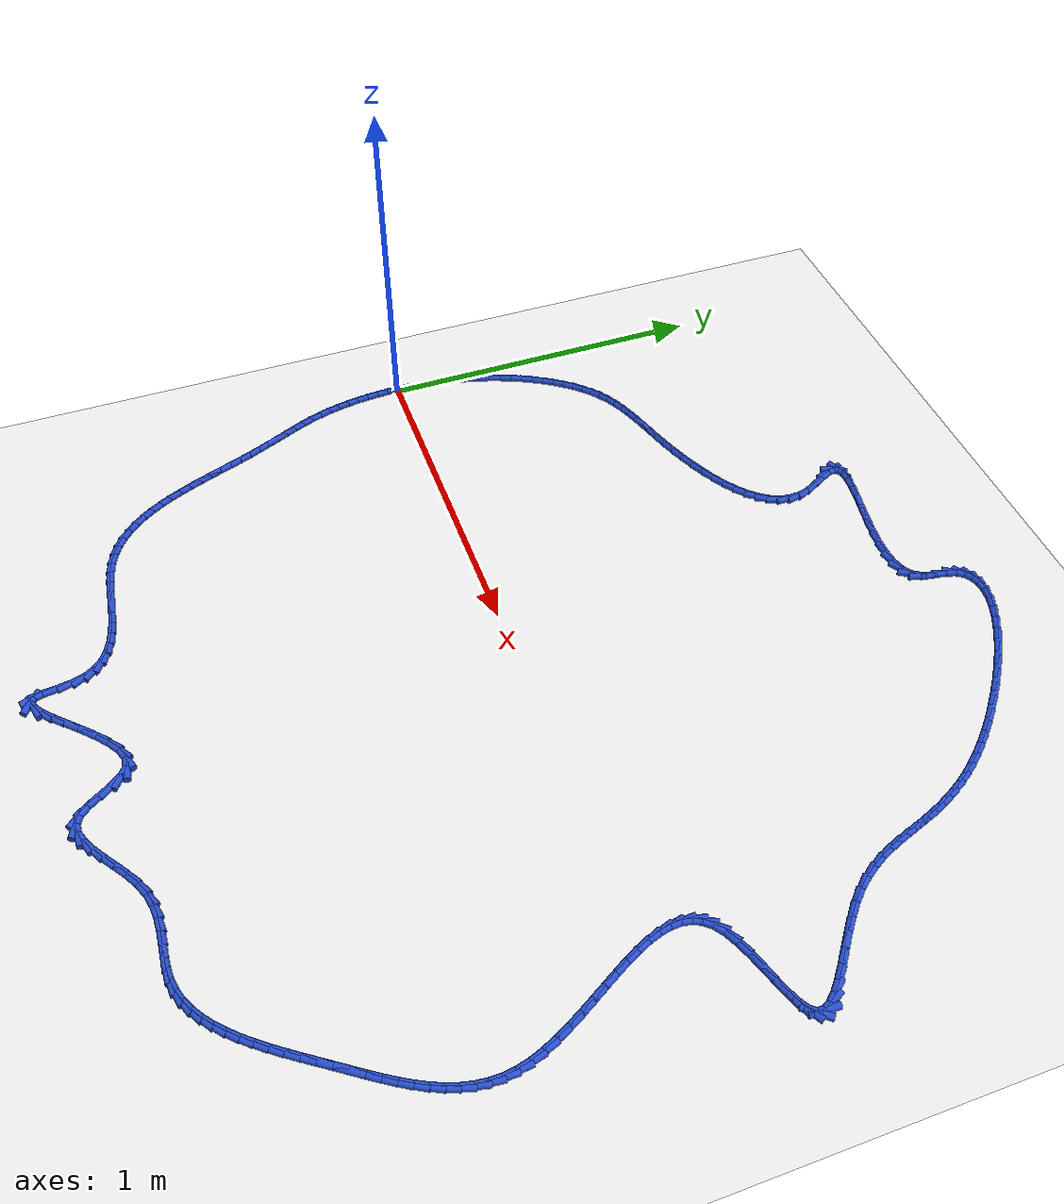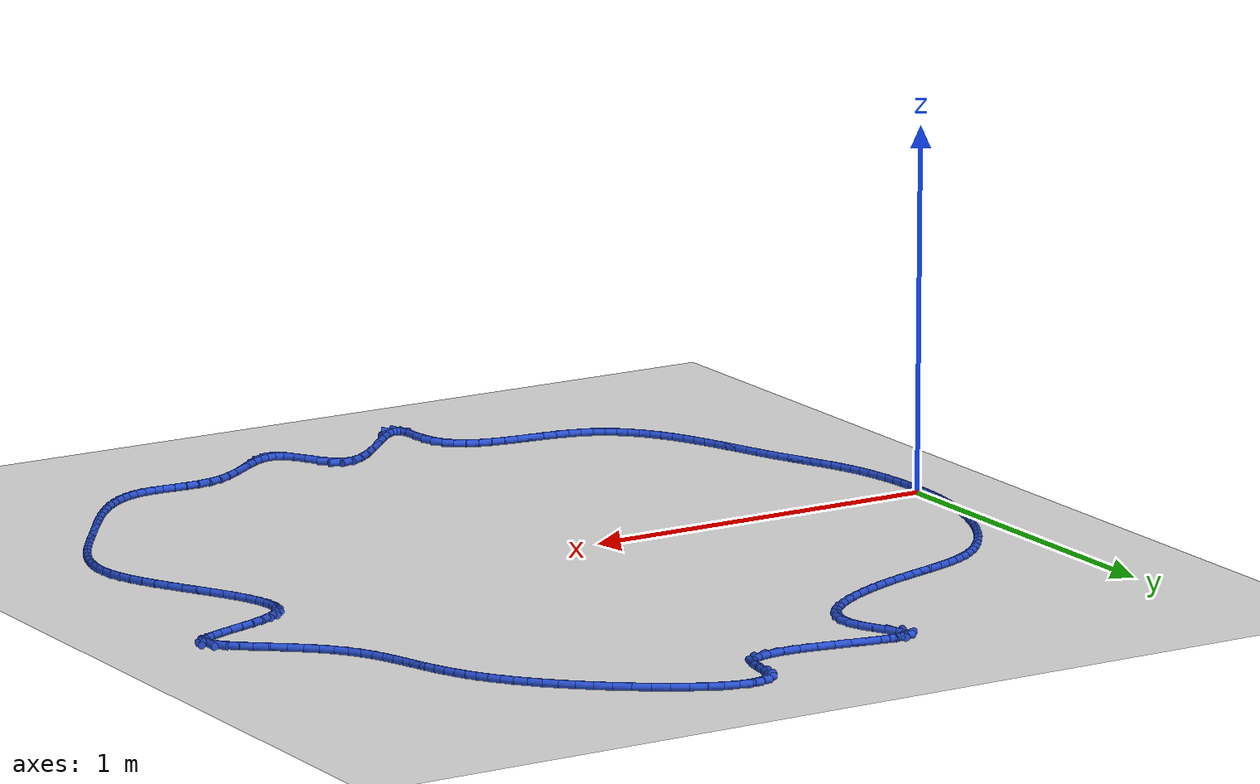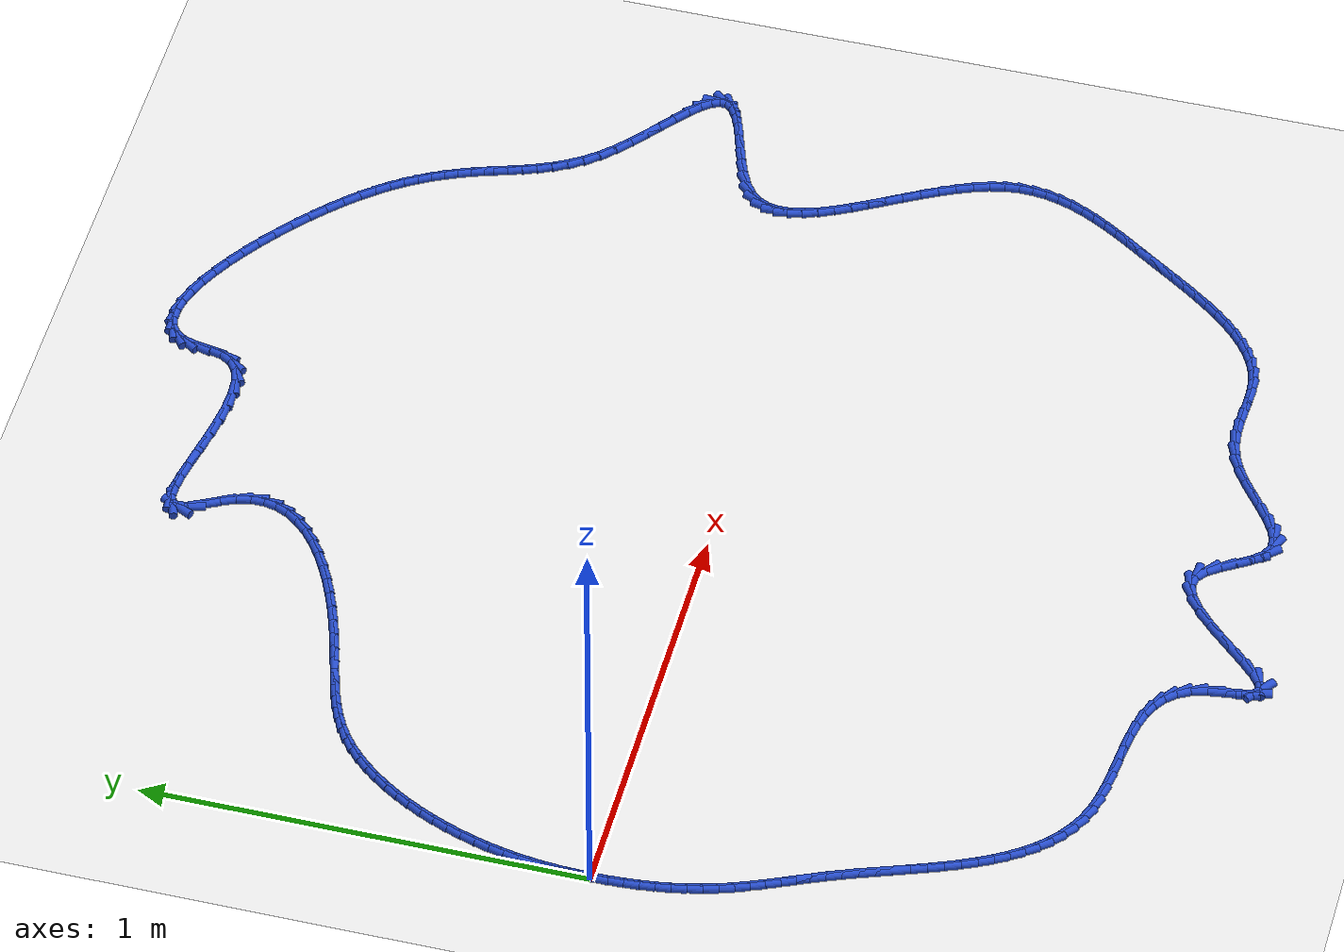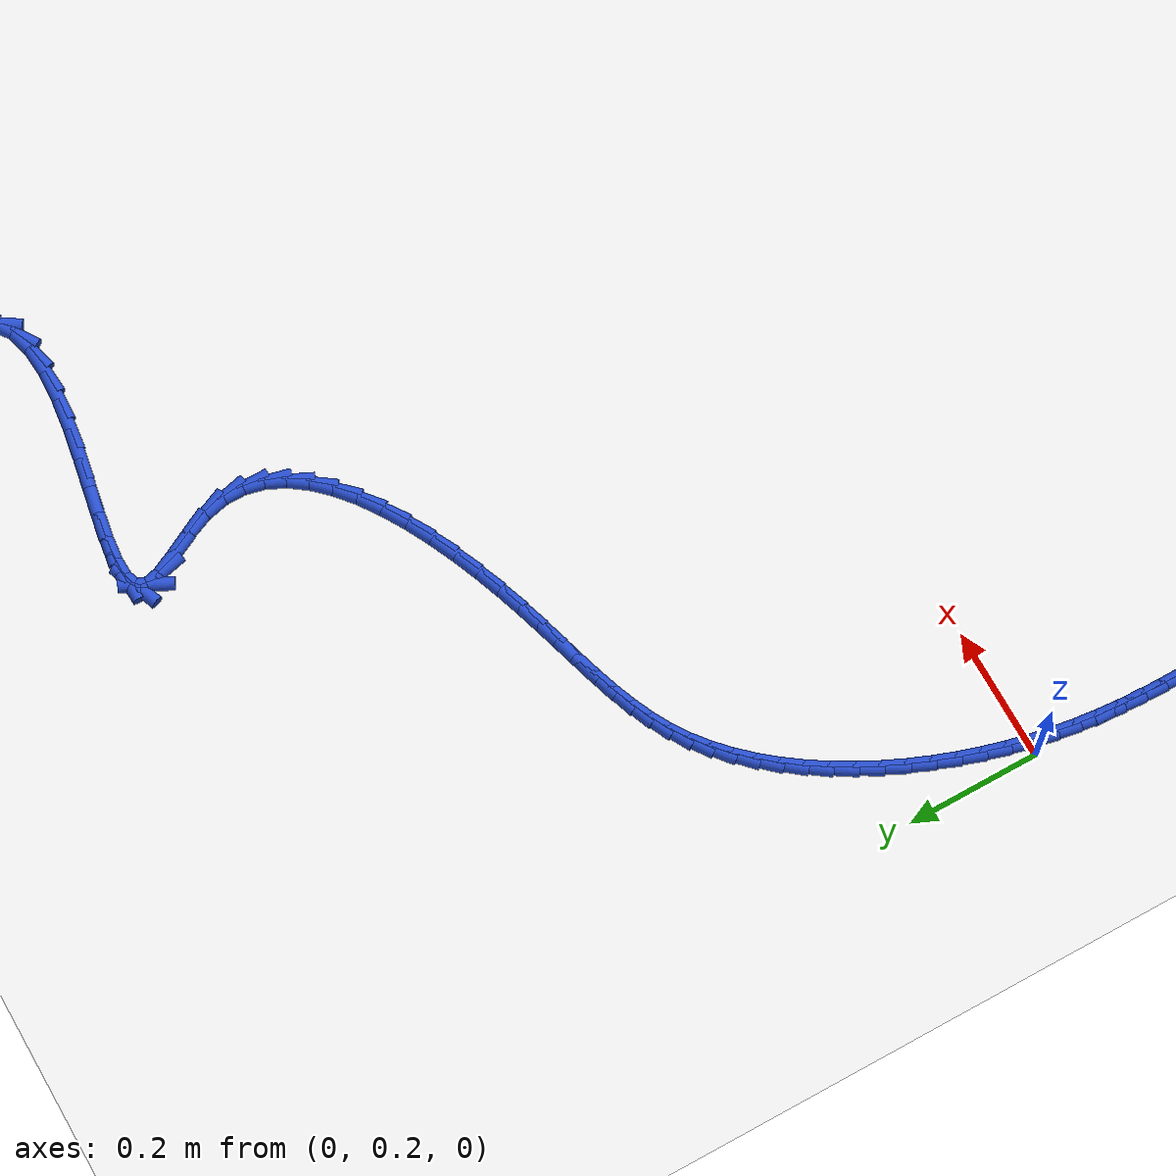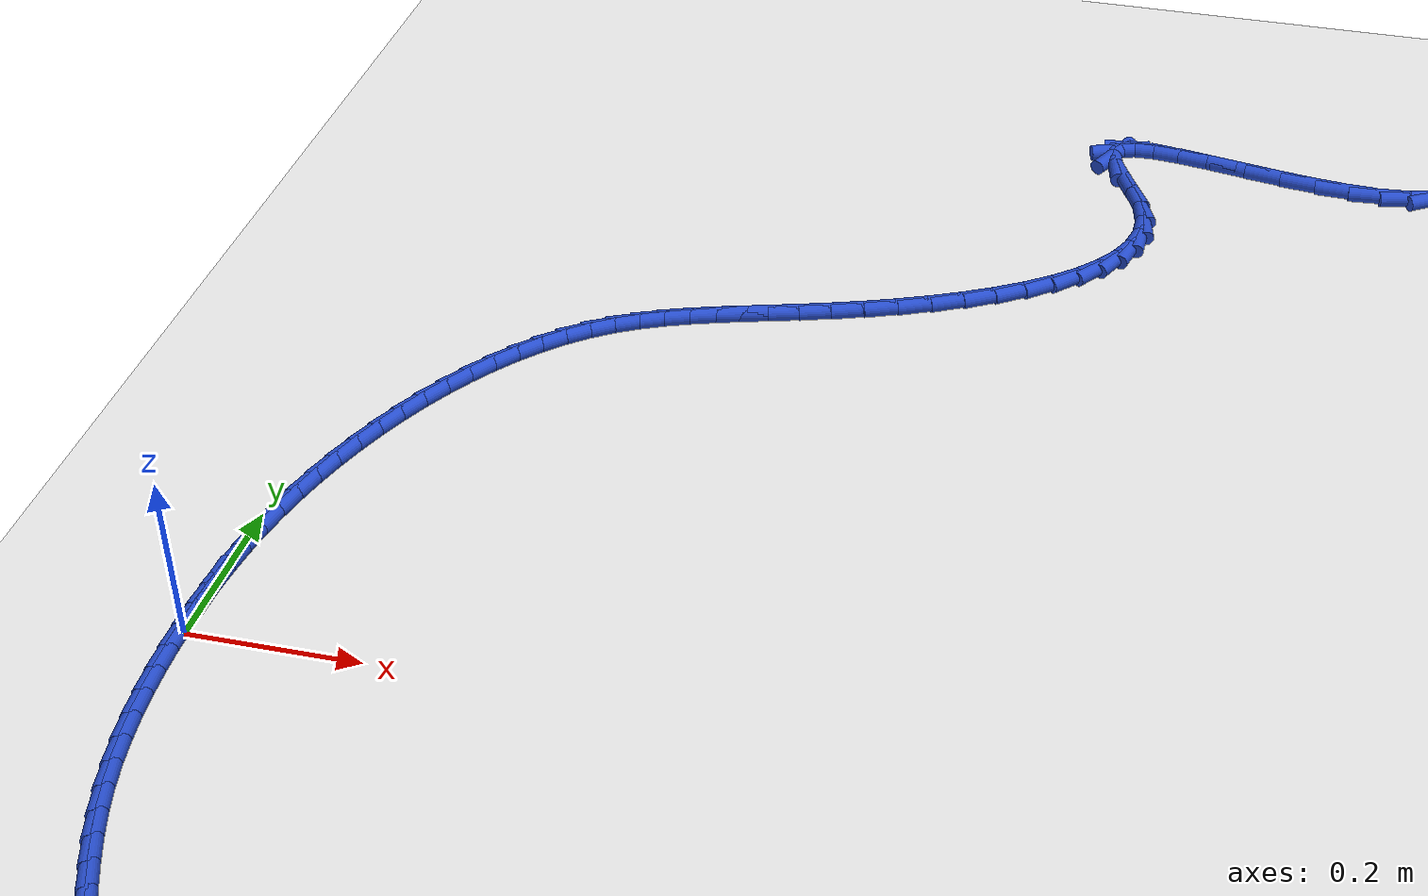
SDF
<sdf version="1.6">
 <world name="default">
  <light name="sun" type="directional">
   <pose>0 0 10 0 -0 0</pose>
   <diffuse>0.8 0.8 0.8 1</diffuse>
   <specular>0.2 0.2 0.2 1</specular>
   <attenuation>
    <range>1000</range>
    <constant>0.9</constant>
    <linear>0.01</linear>
    <quadratic>0.001</quadratic>
   </attenuation>
   <direction>-0.5 0.1 -0.9</direction>
  </light>
  <model name="ground_plane">
   <static>1</static>
   <link name="link">
    <collision name="collision">
     <geometry><plane><normal>0 0 1</normal><size>100 100</size></plane></geometry>
     <surface><friction><ode><mu>100</mu><mu2>50</mu2></ode></friction></surface>
    </collision>
    <visual name="visual">
     <cast_shadows>0</cast_shadows>
     <geometry><plane><normal>0 0 1</normal><size>100 100</size></plane></geometry>
     <material>
      <script><uri>file://media/materials/scripts/gazebo.material</uri><name>Gazebo/WhiteGlow</name></script>
     </material>
    </visual>
   </link>
  </model>
  <gravity>0 0 -9.8</gravity>
  <magnetic_field>6e-06 2.3e-05 -4.2e-05</magnetic_field>
  <atmosphere type="adiabatic"/>
  <physics name="default_physics" default="0" type="ode">
   <max_step_size>0.001</max_step_size>
   <real_time_factor>1</real_time_factor>
   <real_time_update_rate>1000</real_time_update_rate>
  </physics>
  <scene><ambient>0.4 0.4 0.4 1</ambient><background>0.7 0.7 0.7 1</background><shadows>1</shadows></scene>
  <spherical_coordinates>
   <surface_model>EARTH_WGS84</surface_model>
   <latitude_deg>0</latitude_deg>
   <longitude_deg>0</longitude_deg>
   <elevation>0</elevation>
   <heading_deg>0</heading_deg>
  </spherical_coordinates>
  <model name="line">
   <link name="link_0">
    <pose>-9.107298248878237e-18 2.7755575615628914e-17 0.01 0 1.57 1.555257664055114</pose>
    <collision name="collision">
     <geometry><cylinder><radius>0.01</radius><length>0.08</length></cylinder></geometry>
    </collision>
    <visual name="visual">
     <material>
      <script><name>Gazebo/Blue</name><uri>file://media/materials/scripts/gazebo.material</uri></script>
     </material>
     <geometry><cylinder><radius>0.01</radius><length>0.08</length></cylinder></geometry>
    </visual>
   </link>
   <link name="link_1">
    <pose>0.0005190087731679751 0.033398433933696195 0.01 0 1.57 1.5252258439415316</pose>
    <collision name="collision">
     <geometry><cylinder><radius>0.01</radius><length>0.08</length></cylinder></geometry>
    </collision>
    <visual name="visual">
     <material>
      <script><name>Gazebo/Blue</name><uri>file://media/materials/scripts/gazebo.material</uri></script>
     </material>
     <geometry><cylinder><radius>0.01</radius><length>0.08</length></cylinder></geometry>
    </visual>
   </link>
   <link name="link_2">
    <pose>0.0020342389386213155 0.06662566893933405 0.01 0 1.57 1.4930400652777662</pose>
    <collision name="collision">
     <geometry><cylinder><radius>0.01</radius><length>0.08</length></cylinder></geometry>
    </collision>
    <visual name="visual">
     <material>
      <script><name>Gazebo/Blue</name><uri>file://media/materials/scripts/gazebo.material</uri></script>
     </material>
     <geometry><cylinder><radius>0.01</radius><length>0.08</length></cylinder></geometry>
    </visual>
   </link>
   <link name="link_3">
    <pose>0.004613334838291421 0.09972777524075394 0.01 0 1.57 1.4589015401506857</pose>
    <collision name="collision">
     <geometry><cylinder><radius>0.01</radius><length>0.08</length></cylinder></geometry>
    </collision>
    <visual name="visual">
     <material>
      <script><name>Gazebo/Blue</name><uri>file://media/materials/scripts/gazebo.material</uri></script>
     </material>
     <geometry><cylinder><radius>0.01</radius><length>0.08</length></cylinder></geometry>
    </visual>
   </link>
   <link name="link_4">
    <pose>0.008323940814109693 0.13275082306179603 0.01 0 1.57 1.4230552827653005</pose>
    <collision name="collision">
     <geometry><cylinder><radius>0.01</radius><length>0.08</length></cylinder></geometry>
    </collision>
    <visual name="visual">
     <material>
      <script><name>Gazebo/Blue</name><uri>file://media/materials/scripts/gazebo.material</uri></script>
     </material>
     <geometry><cylinder><radius>0.01</radius><length>0.08</length></cylinder></geometry>
    </visual>
   </link>
   <link name="link_5">
    <pose>0.013233701208007547 0.16574088262630074 0.01 0 1.57 1.3857858903296312</pose>
    <collision name="collision">
     <geometry><cylinder><radius>0.01</radius><length>0.08</length></cylinder></geometry>
    </collision>
    <visual name="visual">
     <material>
      <script><name>Gazebo/Blue</name><uri>file://media/materials/scripts/gazebo.material</uri></script>
     </material>
     <geometry><cylinder><radius>0.01</radius><length>0.08</length></cylinder></geometry>
    </visual>
   </link>
   <link name="link_6">
    <pose>0.01941026036191639 0.19874402415810835 0.01 0 1.57 1.3474104782677787</pose>
    <collision name="collision">
     <geometry><cylinder><radius>0.01</radius><length>0.08</length></cylinder></geometry>
    </collision>
    <visual name="visual">
     <material>
      <script><name>Gazebo/Blue</name><uri>file://media/materials/scripts/gazebo.material</uri></script>
     </material>
     <geometry><cylinder><radius>0.01</radius><length>0.08</length></cylinder></geometry>
    </visual>
   </link>
   <link name="link_7">
    <pose>0.02692126261776762 0.23180631788105902 0.01 0 1.57 1.3082696706591057</pose>
    <collision name="collision">
     <geometry><cylinder><radius>0.01</radius><length>0.08</length></cylinder></geometry>
    </collision>
    <visual name="visual">
     <material>
      <script><name>Gazebo/Blue</name><uri>file://media/materials/scripts/gazebo.material</uri></script>
     </material>
     <geometry><cylinder><radius>0.01</radius><length>0.08</length></cylinder></geometry>
    </visual>
   </link>
   <link name="link_8">
    <pose>0.03583425442308479 0.2649735514079297 0.01 0 1.57 1.2687832618331925</pose>
    <collision name="collision">
     <geometry><cylinder><radius>0.01</radius><length>0.08</length></cylinder></geometry>
    </collision>
    <visual name="visual">
     <material>
      <script><name>Gazebo/Blue</name><uri>file://media/materials/scripts/gazebo.material</uri></script>
     </material>
     <geometry><cylinder><radius>0.01</radius><length>0.08</length></cylinder></geometry>
    </visual>
   </link>
   <link name="link_9">
    <pose>0.04619153897217575 0.2982186376818289 0.01 0 1.57 1.2289957124910962</pose>
    <collision name="collision">
     <geometry><cylinder><radius>0.01</radius><length>0.08</length></cylinder></geometry>
    </collision>
    <visual name="visual">
     <material>
      <script><name>Gazebo/Blue</name><uri>file://media/materials/scripts/gazebo.material</uri></script>
     </material>
     <geometry><cylinder><radius>0.01</radius><length>0.08</length></cylinder></geometry>
    </visual>
   </link>
   <link name="link_10">
    <pose>0.057976715418992734 0.3313450171332466 0.01 0 1.57 1.1883586295876978</pose>
    <collision name="collision">
     <geometry><cylinder><radius>0.01</radius><length>0.08</length></cylinder></geometry>
    </collision>
    <visual name="visual">
     <material>
      <script><name>Gazebo/Blue</name><uri>file://media/materials/scripts/gazebo.material</uri></script>
     </material>
     <geometry><cylinder><radius>0.01</radius><length>0.08</length></cylinder></geometry>
    </visual>
   </link>
   <link name="link_11">
    <pose>0.07116505692381593 0.36413209390728146 0.01 0 1.57 1.1462779926022508</pose>
    <collision name="collision">
     <geometry><cylinder><radius>0.01</radius><length>0.08</length></cylinder></geometry>
    </collision>
    <visual name="visual">
     <material>
      <script><name>Gazebo/Blue</name><uri>file://media/materials/scripts/gazebo.material</uri></script>
     </material>
     <geometry><cylinder><radius>0.01</radius><length>0.08</length></cylinder></geometry>
    </visual>
   </link>
   <link name="link_12">
    <pose>0.08573183664692544 0.3963592721490312 0.01 0 1.57 1.102145853257991</pose>
    <collision name="collision">
     <geometry><cylinder><radius>0.01</radius><length>0.08</length></cylinder></geometry>
    </collision>
    <visual name="visual">
     <material>
      <script><name>Gazebo/Blue</name><uri>file://media/materials/scripts/gazebo.material</uri></script>
     </material>
     <geometry><cylinder><radius>0.01</radius><length>0.08</length></cylinder></geometry>
    </visual>
   </link>
   <link name="link_13">
    <pose>0.10165232774860133 0.4278059560035942 0.01 0 1.57 1.055322589953143</pose>
    <collision name="collision">
     <geometry><cylinder><radius>0.01</radius><length>0.08</length></cylinder></geometry>
    </collision>
    <visual name="visual">
     <material>
      <script><name>Gazebo/Blue</name><uri>file://media/materials/scripts/gazebo.material</uri></script>
     </material>
     <geometry><cylinder><radius>0.01</radius><length>0.08</length></cylinder></geometry>
    </visual>
   </link>
   <link name="link_14">
    <pose>0.11890180338912378 0.4582515496160687 0.01 0 1.57 1.0051223816342667</pose>
    <collision name="collision">
     <geometry><cylinder><radius>0.01</radius><length>0.08</length></cylinder></geometry>
    </collision>
    <visual name="visual">
     <material>
      <script><name>Gazebo/Blue</name><uri>file://media/materials/scripts/gazebo.material</uri></script>
     </material>
     <geometry><cylinder><radius>0.01</radius><length>0.08</length></cylinder></geometry>
    </visual>
   </link>
   <link name="link_15">
    <pose>0.13745553672877292 0.4874754571315527 0.01 0 1.57 0.9508032057915508</pose>
    <collision name="collision">
     <geometry><cylinder><radius>0.01</radius><length>0.08</length></cylinder></geometry>
    </collision>
    <visual name="visual">
     <material>
      <script><name>Gazebo/Blue</name><uri>file://media/materials/scripts/gazebo.material</uri></script>
     </material>
     <geometry><cylinder><radius>0.01</radius><length>0.08</length></cylinder></geometry>
    </visual>
   </link>
   <link name="link_16">
    <pose>0.15728880092782888 0.5152570826951446 0.01 0 1.57 0.8915642866965477</pose>
    <collision name="collision">
     <geometry><cylinder><radius>0.01</radius><length>0.08</length></cylinder></geometry>
    </collision>
    <visual name="visual">
     <material>
      <script><name>Gazebo/Blue</name><uri>file://media/materials/scripts/gazebo.material</uri></script>
     </material>
     <geometry><cylinder><radius>0.01</radius><length>0.08</length></cylinder></geometry>
    </visual>
   </link>
   <link name="link_17">
    <pose>0.17837686914657175 0.5413758304519423 0.01 0 1.57 0.8265561721535755</pose>
    <collision name="collision">
     <geometry><cylinder><radius>0.01</radius><length>0.08</length></cylinder></geometry>
    </collision>
    <visual name="visual">
     <material>
      <script><name>Gazebo/Blue</name><uri>file://media/materials/scripts/gazebo.material</uri></script>
     </material>
     <geometry><cylinder><radius>0.01</radius><length>0.08</length></cylinder></geometry>
    </visual>
   </link>
   <link name="link_18">
    <pose>0.2006950145452817 0.5656111045470443 0.01 0 1.57 0.754911493349275</pose>
    <collision name="collision">
     <geometry><cylinder><radius>0.01</radius><length>0.08</length></cylinder></geometry>
    </collision>
    <visual name="visual">
     <material>
      <script><name>Gazebo/Blue</name><uri>file://media/materials/scripts/gazebo.material</uri></script>
     </material>
     <geometry><cylinder><radius>0.01</radius><length>0.08</length></cylinder></geometry>
    </visual>
   </link>
   <link name="link_19">
    <pose>0.22421851028423884 0.5877423091255484 0.01 0 1.57 0.6758073908442525</pose>
    <collision name="collision">
     <geometry><cylinder><radius>0.01</radius><length>0.08</length></cylinder></geometry>
    </collision>
    <visual name="visual">
     <material>
      <script><name>Gazebo/Blue</name><uri>file://media/materials/scripts/gazebo.material</uri></script>
     </material>
     <geometry><cylinder><radius>0.01</radius><length>0.08</length></cylinder></geometry>
    </visual>
   </link>
   <link name="link_20">
    <pose>0.2489226295237232 0.6075488483325528 0.01 0 1.57 0.5888493216553347</pose>
    <collision name="collision">
     <geometry><cylinder><radius>0.01</radius><length>0.08</length></cylinder></geometry>
    </collision>
    <visual name="visual">
     <material>
      <script><name>Gazebo/Blue</name><uri>file://media/materials/scripts/gazebo.material</uri></script>
     </material>
     <geometry><cylinder><radius>0.01</radius><length>0.08</length></cylinder></geometry>
    </visual>
   </link>
   <link name="link_21">
    <pose>0.274783455820922 0.6248210458230733 0.01 0 1.57 0.5023941022503997</pose>
    <collision name="collision">
     <geometry><cylinder><radius>0.01</radius><length>0.08</length></cylinder></geometry>
    </collision>
    <visual name="visual">
     <material>
      <script><name>Gazebo/Blue</name><uri>file://media/materials/scripts/gazebo.material</uri></script>
     </material>
     <geometry><cylinder><radius>0.01</radius><length>0.08</length></cylinder></geometry>
    </visual>
   </link>
   <link name="link_22">
    <pose>0.30180047906041185 0.6396646085191082 0.01 0 1.57 0.4283507575286829</pose>
    <collision name="collision">
     <geometry><cylinder><radius>0.01</radius><length>0.08</length></cylinder></geometry>
    </collision>
    <visual name="visual">
     <material>
      <script><name>Gazebo/Blue</name><uri>file://media/materials/scripts/gazebo.material</uri></script>
     </material>
     <geometry><cylinder><radius>0.01</radius><length>0.08</length></cylinder></geometry>
    </visual>
   </link>
   <link name="link_23">
    <pose>0.3299995969917477 0.6525410701493269 0.01 0 1.57 0.36951092484150055</pose>
    <collision name="collision">
     <geometry><cylinder><radius>0.01</radius><length>0.08</length></cylinder></geometry>
    </collision>
    <visual name="visual">
     <material>
      <script><name>Gazebo/Blue</name><uri>file://media/materials/scripts/gazebo.material</uri></script>
     </material>
     <geometry><cylinder><radius>0.01</radius><length>0.08</length></cylinder></geometry>
    </visual>
   </link>
   <link name="link_24">
    <pose>0.3594081208097713 0.6639310095913754 0.01 0 1.57 0.32670310271949693</pose>
    <collision name="collision">
     <geometry><cylinder><radius>0.01</radius><length>0.08</length></cylinder></geometry>
    </collision>
    <visual name="visual">
     <material>
      <script><name>Gazebo/Blue</name><uri>file://media/materials/scripts/gazebo.material</uri></script>
     </material>
     <geometry><cylinder><radius>0.01</radius><length>0.08</length></cylinder></geometry>
    </visual>
   </link>
   <link name="link_25">
    <pose>0.39005336170932364 0.6743150057228985 0.01 0 1.57 0.29965496754526444</pose>
    <collision name="collision">
     <geometry><cylinder><radius>0.01</radius><length>0.08</length></cylinder></geometry>
    </collision>
    <visual name="visual">
     <material>
      <script><name>Gazebo/Blue</name><uri>file://media/materials/scripts/gazebo.material</uri></script>
     </material>
     <geometry><cylinder><radius>0.01</radius><length>0.08</length></cylinder></geometry>
    </visual>
   </link>
   <link name="link_26">
    <pose>0.42196263088524644 0.6841736374215424 0.01 0 1.57 0.28740819542487617</pose>
    <collision name="collision">
     <geometry><cylinder><radius>0.01</radius><length>0.08</length></cylinder></geometry>
    </collision>
    <visual name="visual">
     <material>
      <script><name>Gazebo/Blue</name><uri>file://media/materials/scripts/gazebo.material</uri></script>
     </material>
     <geometry><cylinder><radius>0.01</radius><length>0.08</length></cylinder></geometry>
    </visual>
   </link>
   <link name="link_27">
    <pose>0.45516323953238114 0.6939874835649525 0.01 0 1.57 0.2886335349314423</pose>
    <collision name="collision">
     <geometry><cylinder><radius>0.01</radius><length>0.08</length></cylinder></geometry>
    </collision>
    <visual name="visual">
     <material>
      <script><name>Gazebo/Blue</name><uri>file://media/materials/scripts/gazebo.material</uri></script>
     </material>
     <geometry><cylinder><radius>0.01</radius><length>0.08</length></cylinder></geometry>
    </visual>
   </link>
   <link name="link_28">
    <pose>0.489682498845569 0.7042371230307742 0.01 0 1.57 0.3018209537267275</pose>
    <collision name="collision">
     <geometry><cylinder><radius>0.01</radius><length>0.08</length></cylinder></geometry>
    </collision>
    <visual name="visual">
     <material>
      <script><name>Gazebo/Blue</name><uri>file://media/materials/scripts/gazebo.material</uri></script>
     </material>
     <geometry><cylinder><radius>0.01</radius><length>0.08</length></cylinder></geometry>
    </visual>
   </link>
   <link name="link_29">
    <pose>0.525547720019652 0.7154031346966535 0.01 0 1.57 0.32516992643794584</pose>
    <collision name="collision">
     <geometry><cylinder><radius>0.01</radius><length>0.08</length></cylinder></geometry>
    </collision>
    <visual name="visual">
     <material>
      <script><name>Gazebo/Blue</name><uri>file://media/materials/scripts/gazebo.material</uri></script>
     </material>
     <geometry><cylinder><radius>0.01</radius><length>0.08</length></cylinder></geometry>
    </visual>
   </link>
   <link name="link_30">
    <pose>0.562756377461712 0.7279475493120858 0.01 0 1.57 0.3547476634860732</pose>
    <collision name="collision">
     <geometry><cylinder><radius>0.01</radius><length>0.08</length></cylinder></geometry>
    </collision>
    <visual name="visual">
     <material>
      <script><name>Gazebo/Blue</name><uri>file://media/materials/scripts/gazebo.material</uri></script>
     </material>
     <geometry><cylinder><radius>0.01</radius><length>0.08</length></cylinder></geometry>
    </visual>
   </link>
   <link name="link_31">
    <pose>0.6008864624210706 0.7420716246697212 0.01 0 1.57 0.3891275390165753</pose>
    <collision name="collision">
     <geometry><cylinder><radius>0.01</radius><length>0.08</length></cylinder></geometry>
    </collision>
    <visual name="visual">
     <material>
      <script><name>Gazebo/Blue</name><uri>file://media/materials/scripts/gazebo.material</uri></script>
     </material>
     <geometry><cylinder><radius>0.01</radius><length>0.08</length></cylinder></geometry>
    </visual>
   </link>
   <link name="link_32">
    <pose>0.6392063049287038 0.7577841167417315 0.01 0 1.57 0.4296222060591775</pose>
    <collision name="collision">
     <geometry><cylinder><radius>0.01</radius><length>0.08</length></cylinder></geometry>
    </collision>
    <visual name="visual">
     <material>
      <script><name>Gazebo/Blue</name><uri>file://media/materials/scripts/gazebo.material</uri></script>
     </material>
     <geometry><cylinder><radius>0.01</radius><length>0.08</length></cylinder></geometry>
    </visual>
   </link>
   <link name="link_33">
    <pose>0.6769769989883767 0.7750892832023798 0.01 0 1.57 0.4780321088434812</pose>
    <collision name="collision">
     <geometry><cylinder><radius>0.01</radius><length>0.08</length></cylinder></geometry>
    </collision>
    <visual name="visual">
     <material>
      <script><name>Gazebo/Blue</name><uri>file://media/materials/scripts/gazebo.material</uri></script>
     </material>
     <geometry><cylinder><radius>0.01</radius><length>0.08</length></cylinder></geometry>
    </visual>
   </link>
   <link name="link_34">
    <pose>0.7134596386038544 0.7939913817259285 0.01 0 1.57 0.5367811975345802</pose>
    <collision name="collision">
     <geometry><cylinder><radius>0.01</radius><length>0.08</length></cylinder></geometry>
    </collision>
    <visual name="visual">
     <material>
      <script><name>Gazebo/Blue</name><uri>file://media/materials/scripts/gazebo.material</uri></script>
     </material>
     <geometry><cylinder><radius>0.01</radius><length>0.08</length></cylinder></geometry>
    </visual>
   </link>
   <link name="link_35">
    <pose>0.7479153177789027 0.814494669986641 0.01 0 1.57 0.609154211488663</pose>
    <collision name="collision">
     <geometry><cylinder><radius>0.01</radius><length>0.08</length></cylinder></geometry>
    </collision>
    <visual name="visual">
     <material>
      <script><name>Gazebo/Blue</name><uri>file://media/materials/scripts/gazebo.material</uri></script>
     </material>
     <geometry><cylinder><radius>0.01</radius><length>0.08</length></cylinder></geometry>
    </visual>
   </link>
   <link name="link_36">
    <pose>0.7796051305172867 0.83660340565878 0.01 0 1.57 0.6995537803106278</pose>
    <collision name="collision">
     <geometry><cylinder><radius>0.01</radius><length>0.08</length></cylinder></geometry>
    </collision>
    <visual name="visual">
     <material>
      <script><name>Gazebo/Blue</name><uri>file://media/materials/scripts/gazebo.material</uri></script>
     </material>
     <geometry><cylinder><radius>0.01</radius><length>0.08</length></cylinder></geometry>
    </visual>
   </link>
   <link name="link_37">
    <pose>0.8077901708227724 0.8603218464166089 0.01 0 1.57 0.8136215447781497</pose>
    <collision name="collision">
     <geometry><cylinder><radius>0.01</radius><length>0.08</length></cylinder></geometry>
    </collision>
    <visual name="visual">
     <material>
      <script><name>Gazebo/Blue</name><uri>file://media/materials/scripts/gazebo.material</uri></script>
     </material>
     <geometry><cylinder><radius>0.01</radius><length>0.08</length></cylinder></geometry>
    </visual>
   </link>
   <link name="link_38">
    <pose>0.8317315326991243 0.8856542499343899 0.01 0 1.57 0.9577497156196378</pose>
    <collision name="collision">
     <geometry><cylinder><radius>0.01</radius><length>0.08</length></cylinder></geometry>
    </collision>
    <visual name="visual">
     <material>
      <script><name>Gazebo/Blue</name><uri>file://media/materials/scripts/gazebo.material</uri></script>
     </material>
     <geometry><cylinder><radius>0.01</radius><length>0.08</length></cylinder></geometry>
    </visual>
   </link>
   <link name="link_39">
    <pose>0.8506903101501084 0.9126048738863863 0.01 0 1.57 1.1369555155943236</pose>
    <collision name="collision">
     <geometry><cylinder><radius>0.01</radius><length>0.08</length></cylinder></geometry>
    </collision>
    <visual name="visual">
     <material>
      <script><name>Gazebo/Blue</name><uri>file://media/materials/scripts/gazebo.material</uri></script>
     </material>
     <geometry><cylinder><radius>0.01</radius><length>0.08</length></cylinder></geometry>
    </visual>
   </link>
   <link name="link_40">
    <pose>0.8639275971794897 0.9411779759468609 0.01 0 1.57 1.350051564740795</pose>
    <collision name="collision">
     <geometry><cylinder><radius>0.01</radius><length>0.08</length></cylinder></geometry>
    </collision>
    <visual name="visual">
     <material>
      <script><name>Gazebo/Blue</name><uri>file://media/materials/scripts/gazebo.material</uri></script>
     </material>
     <geometry><cylinder><radius>0.01</radius><length>0.08</length></cylinder></geometry>
    </visual>
   </link>
   <link name="link_41">
    <pose>0.8707044877910336 0.9713778137900764 0.01 0 1.57 -1.5575265819794573</pose>
    <collision name="collision">
     <geometry><cylinder><radius>0.01</radius><length>0.08</length></cylinder></geometry>
    </collision>
    <visual name="visual">
     <material>
      <script><name>Gazebo/Blue</name><uri>file://media/materials/scripts/gazebo.material</uri></script>
     </material>
     <geometry><cylinder><radius>0.01</radius><length>0.08</length></cylinder></geometry>
    </visual>
   </link>
   <link name="link_42">
    <pose>0.8702820759885058 1.0032086450902962 0.01 0 1.57 -1.3261108181710088</pose>
    <collision name="collision">
     <geometry><cylinder><radius>0.01</radius><length>0.08</length></cylinder></geometry>
    </collision>
    <visual name="visual">
     <material>
      <script><name>Gazebo/Blue</name><uri>file://media/materials/scripts/gazebo.material</uri></script>
     </material>
     <geometry><cylinder><radius>0.01</radius><length>0.08</length></cylinder></geometry>
    </visual>
   </link>
   <link name="link_43">
    <pose>0.861926518027787 1.036672566801154 0.01 0 1.57 -1.1503029712033523</pose>
    <collision name="collision">
     <geometry><cylinder><radius>0.01</radius><length>0.08</length></cylinder></geometry>
    </collision>
    <visual name="visual">
     <material>
      <script><name>Gazebo/Blue</name><uri>file://media/materials/scripts/gazebo.material</uri></script>
     </material>
     <geometry><cylinder><radius>0.01</radius><length>0.08</length></cylinder></geometry>
    </visual>
   </link>
   <link name="link_44">
    <pose>0.8465445765529488 1.0710714159947974 0.01 0 1.57 -1.0820534770450037</pose>
    <collision name="collision">
     <geometry><cylinder><radius>0.01</radius><length>0.08</length></cylinder></geometry>
    </collision>
    <visual name="visual">
     <material>
      <script><name>Gazebo/Blue</name><uri>file://media/materials/scripts/gazebo.material</uri></script>
     </material>
     <geometry><cylinder><radius>0.01</radius><length>0.08</length></cylinder></geometry>
    </visual>
   </link>
   <link name="link_45">
    <pose>0.8290315501520201 1.1040046032945137 0.01 0 1.57 -1.1141775698686194</pose>
    <collision name="collision">
     <geometry><cylinder><radius>0.01</radius><length>0.08</length></cylinder></geometry>
    </collision>
    <visual name="visual">
     <material>
      <script><name>Gazebo/Blue</name><uri>file://media/materials/scripts/gazebo.material</uri></script>
     </material>
     <geometry><cylinder><radius>0.01</radius><length>0.08</length></cylinder></geometry>
    </visual>
   </link>
   <link name="link_46">
    <pose>0.8148772272950504 1.1328177932591332 0.01 0 1.57 -1.3338683731112164</pose>
    <collision name="collision">
     <geometry><cylinder><radius>0.01</radius><length>0.08</length></cylinder></geometry>
    </collision>
    <visual name="visual">
     <material>
      <script><name>Gazebo/Blue</name><uri>file://media/materials/scripts/gazebo.material</uri></script>
     </material>
     <geometry><cylinder><radius>0.01</radius><length>0.08</length></cylinder></geometry>
    </visual>
   </link>
   <link name="link_47">
    <pose>0.8095532159255139 1.1548667562507464 0.01 0 1.57 1.119879310825265</pose>
    <collision name="collision">
     <geometry><cylinder><radius>0.01</radius><length>0.08</length></cylinder></geometry>
    </collision>
    <visual name="visual">
     <material>
      <script><name>Gazebo/Blue</name><uri>file://media/materials/scripts/gazebo.material</uri></script>
     </material>
     <geometry><cylinder><radius>0.01</radius><length>0.08</length></cylinder></geometry>
    </visual>
   </link>
   <link name="link_48">
    <pose>0.8162795628326202 1.1687588124125254 0.01 0 1.57 0.368221571323874</pose>
    <collision name="collision">
     <geometry><cylinder><radius>0.01</radius><length>0.08</length></cylinder></geometry>
    </collision>
    <visual name="visual">
     <material>
      <script><name>Gazebo/Blue</name><uri>file://media/materials/scripts/gazebo.material</uri></script>
     </material>
     <geometry><cylinder><radius>0.01</radius><length>0.08</length></cylinder></geometry>
    </visual>
   </link>
   <link name="link_49">
    <pose>0.8338753520867683 1.1755475951564798 0.01 0 1.57 0.038166733122667724</pose>
    <collision name="collision">
     <geometry><cylinder><radius>0.01</radius><length>0.08</length></cylinder></geometry>
    </collision>
    <visual name="visual">
     <material>
      <script><name>Gazebo/Blue</name><uri>file://media/materials/scripts/gazebo.material</uri></script>
     </material>
     <geometry><cylinder><radius>0.01</radius><length>0.08</length></cylinder></geometry>
    </visual>
   </link>
   <link name="link_50">
    <pose>0.8606500818916818 1.1765699956150115 0.01 0 1.57 -0.09911304540920102</pose>
    <collision name="collision">
     <geometry><cylinder><radius>0.01</radius><length>0.08</length></cylinder></geometry>
    </collision>
    <visual name="visual">
     <material>
      <script><name>Gazebo/Blue</name><uri>file://media/materials/scripts/gazebo.material</uri></script>
     </material>
     <geometry><cylinder><radius>0.01</radius><length>0.08</length></cylinder></geometry>
    </visual>
   </link>
   <link name="link_51">
    <pose>0.894913250451083 1.1731629049205237 0.01 0 1.57 -0.16084288697112148</pose>
    <collision name="collision">
     <geometry><cylinder><radius>0.01</radius><length>0.08</length></cylinder></geometry>
    </collision>
    <visual name="visual">
     <material>
      <script><name>Gazebo/Blue</name><uri>file://media/materials/scripts/gazebo.material</uri></script>
     </material>
     <geometry><cylinder><radius>0.01</radius><length>0.08</length></cylinder></geometry>
    </visual>
   </link>
   <link name="link_52">
    <pose>0.9349743559686962 1.166663214205418 0.01 0 1.57 -0.1847748131101139</pose>
    <collision name="collision">
     <geometry><cylinder><radius>0.01</radius><length>0.08</length></cylinder></geometry>
    </collision>
    <visual name="visual">
     <material>
      <script><name>Gazebo/Blue</name><uri>file://media/materials/scripts/gazebo.material</uri></script>
     </material>
     <geometry><cylinder><radius>0.01</radius><length>0.08</length></cylinder></geometry>
    </visual>
   </link>
   <link name="link_53">
    <pose>0.9791428966482425 1.1584078146020962 0.01 0 1.57 -0.18409184921344965</pose>
    <collision name="collision">
     <geometry><cylinder><radius>0.01</radius><length>0.08</length></cylinder></geometry>
    </collision>
    <visual name="visual">
     <material>
      <script><name>Gazebo/Blue</name><uri>file://media/materials/scripts/gazebo.material</uri></script>
     </material>
     <geometry><cylinder><radius>0.01</radius><length>0.08</length></cylinder></geometry>
    </visual>
   </link>
   <link name="link_54">
    <pose>1.0257283706934461 1.1497335972429616 0.01 0 1.57 -0.16249104160121441</pose>
    <collision name="collision">
     <geometry><cylinder><radius>0.01</radius><length>0.08</length></cylinder></geometry>
    </collision>
    <visual name="visual">
     <material>
      <script><name>Gazebo/Blue</name><uri>file://media/materials/scripts/gazebo.material</uri></script>
     </material>
     <geometry><cylinder><radius>0.01</radius><length>0.08</length></cylinder></geometry>
    </visual>
   </link>
   <link name="link_55">
    <pose>1.07304027630803 1.1419774532604159 0.01 0 1.57 -0.11814061830069224</pose>
    <collision name="collision">
     <geometry><cylinder><radius>0.01</radius><length>0.08</length></cylinder></geometry>
    </collision>
    <visual name="visual">
     <material>
      <script><name>Gazebo/Blue</name><uri>file://media/materials/scripts/gazebo.material</uri></script>
     </material>
     <geometry><cylinder><radius>0.01</radius><length>0.08</length></cylinder></geometry>
    </visual>
   </link>
   <link name="link_56">
    <pose>1.119388111695717 1.1364762737868612 0.01 0 1.57 -0.04367057439949822</pose>
    <collision name="collision">
     <geometry><cylinder><radius>0.01</radius><length>0.08</length></cylinder></geometry>
    </collision>
    <visual name="visual">
     <material>
      <script><name>Gazebo/Blue</name><uri>file://media/materials/scripts/gazebo.material</uri></script>
     </material>
     <geometry><cylinder><radius>0.01</radius><length>0.08</length></cylinder></geometry>
    </visual>
   </link>
   <link name="link_57">
    <pose>1.1630813750602293 1.1345669499547002 0.01 0 1.57 0.07658591892966146</pose>
    <collision name="collision">
     <geometry><cylinder><radius>0.01</radius><length>0.08</length></cylinder></geometry>
    </collision>
    <visual name="visual">
     <material>
      <script><name>Gazebo/Blue</name><uri>file://media/materials/scripts/gazebo.material</uri></script>
     </material>
     <geometry><cylinder><radius>0.01</radius><length>0.08</length></cylinder></geometry>
    </visual>
   </link>
   <link name="link_58">
    <pose>1.2024295646052916 1.137586372896335 0.01 0 1.57 0.2718260754717742</pose>
    <collision name="collision">
     <geometry><cylinder><radius>0.01</radius><length>0.08</length></cylinder></geometry>
    </collision>
    <visual name="visual">
     <material>
      <script><name>Gazebo/Blue</name><uri>file://media/materials/scripts/gazebo.material</uri></script>
     </material>
     <geometry><cylinder><radius>0.01</radius><length>0.08</length></cylinder></geometry>
    </visual>
   </link>
   <link name="link_59">
    <pose>1.2357421785346252 1.1468714337441674 0.01 0 1.57 0.5833859597466695</pose>
    <collision name="collision">
     <geometry><cylinder><radius>0.01</radius><length>0.08</length></cylinder></geometry>
    </collision>
    <visual name="visual">
     <material>
      <script><name>Gazebo/Blue</name><uri>file://media/materials/scripts/gazebo.material</uri></script>
     </material>
     <geometry><cylinder><radius>0.01</radius><length>0.08</length></cylinder></geometry>
    </visual>
   </link>
   <link name="link_60">
    <pose>1.2613287150519539 1.1637590236306004 0.01 0 1.57 1.0088539453718253</pose>
    <collision name="collision">
     <geometry><cylinder><radius>0.01</radius><length>0.08</length></cylinder></geometry>
    </collision>
    <visual name="visual">
     <material>
      <script><name>Gazebo/Blue</name><uri>file://media/materials/scripts/gazebo.material</uri></script>
     </material>
     <geometry><cylinder><radius>0.01</radius><length>0.08</length></cylinder></geometry>
    </visual>
   </link>
   <link name="link_61">
    <pose>1.2775546202799208 1.1895283890998463 0.01 0 1.57 1.3288996908937807</pose>
    <collision name="collision">
     <geometry><cylinder><radius>0.01</radius><length>0.08</length></cylinder></geometry>
    </collision>
    <visual name="visual">
     <material>
      <script><name>Gazebo/Blue</name><uri>file://media/materials/scripts/gazebo.material</uri></script>
     </material>
     <geometry><cylinder><radius>0.01</radius><length>0.08</length></cylinder></geometry>
    </visual>
   </link>
   <link name="link_62">
    <pose>1.285683026691469 1.222473215488724 0.01 0 1.57 1.409470532503863</pose>
    <collision name="collision">
     <geometry><cylinder><radius>0.01</radius><length>0.08</length></cylinder></geometry>
    </collision>
    <visual name="visual">
     <material>
      <script><name>Gazebo/Blue</name><uri>file://media/materials/scripts/gazebo.material</uri></script>
     </material>
     <geometry><cylinder><radius>0.01</radius><length>0.08</length></cylinder></geometry>
    </visual>
   </link>
   <link name="link_63">
    <pose>1.2912226414353776 1.2565128627161324 0.01 0 1.57 1.2814580584756001</pose>
    <collision name="collision">
     <geometry><cylinder><radius>0.01</radius><length>0.08</length></cylinder></geometry>
    </collision>
    <visual name="visual">
     <material>
      <script><name>Gazebo/Blue</name><uri>file://media/materials/scripts/gazebo.material</uri></script>
     </material>
     <geometry><cylinder><radius>0.01</radius><length>0.08</length></cylinder></geometry>
    </visual>
   </link>
   <link name="link_64">
    <pose>1.299829876585776 1.285426059414801 0.01 0 1.57 0.986004935253308</pose>
    <collision name="collision">
     <geometry><cylinder><radius>0.01</radius><length>0.08</length></cylinder></geometry>
    </collision>
    <visual name="visual">
     <material>
      <script><name>Gazebo/Blue</name><uri>file://media/materials/scripts/gazebo.material</uri></script>
     </material>
     <geometry><cylinder><radius>0.01</radius><length>0.08</length></cylinder></geometry>
    </visual>
   </link>
   <link name="link_65">
    <pose>1.3138503569327997 1.3066038125582822 0.01 0 1.57 0.6323115348763421</pose>
    <collision name="collision">
     <geometry><cylinder><radius>0.01</radius><length>0.08</length></cylinder></geometry>
    </collision>
    <visual name="visual">
     <material>
      <script><name>Gazebo/Blue</name><uri>file://media/materials/scripts/gazebo.material</uri></script>
     </material>
     <geometry><cylinder><radius>0.01</radius><length>0.08</length></cylinder></geometry>
    </visual>
   </link>
   <link name="link_66">
    <pose>1.3328203102232936 1.320502358994393 0.01 0 1.57 0.2978365182773539</pose>
    <collision name="collision">
     <geometry><cylinder><radius>0.01</radius><length>0.08</length></cylinder></geometry>
    </collision>
    <visual name="visual">
     <material>
      <script><name>Gazebo/Blue</name><uri>file://media/materials/scripts/gazebo.material</uri></script>
     </material>
     <geometry><cylinder><radius>0.01</radius><length>0.08</length></cylinder></geometry>
    </visual>
   </link>
   <link name="link_67">
    <pose>1.3561868797001355 1.3276751323995513 0.01 0 1.57 0.036750148334386425</pose>
    <collision name="collision">
     <geometry><cylinder><radius>0.01</radius><length>0.08</length></cylinder></geometry>
    </collision>
    <visual name="visual">
     <material>
      <script><name>Gazebo/Blue</name><uri>file://media/materials/scripts/gazebo.material</uri></script>
     </material>
     <geometry><cylinder><radius>0.01</radius><length>0.08</length></cylinder></geometry>
    </visual>
   </link>
   <link name="link_68">
    <pose>1.3833972086062052 1.328675566450174 0.01 0 1.57 -0.15027761381971538</pose>
    <collision name="collision">
     <geometry><cylinder><radius>0.01</radius><length>0.08</length></cylinder></geometry>
    </collision>
    <visual name="visual">
     <material>
      <script><name>Gazebo/Blue</name><uri>file://media/materials/scripts/gazebo.material</uri></script>
     </material>
     <geometry><cylinder><radius>0.01</radius><length>0.08</length></cylinder></geometry>
    </visual>
   </link>
   <link name="link_69">
    <pose>1.4138984401843804 1.3240570948226789 0.01 0 1.57 -0.28349337409361886</pose>
    <collision name="collision">
     <geometry><cylinder><radius>0.01</radius><length>0.08</length></cylinder></geometry>
    </collision>
    <visual name="visual">
     <material>
      <script><name>Gazebo/Blue</name><uri>file://media/materials/scripts/gazebo.material</uri></script>
     </material>
     <geometry><cylinder><radius>0.01</radius><length>0.08</length></cylinder></geometry>
    </visual>
   </link>
   <link name="link_70">
    <pose>1.447137717677542 1.3143731511934837 0.01 0 1.57 -0.3811436877735063</pose>
    <collision name="collision">
     <geometry><cylinder><radius>0.01</radius><length>0.08</length></cylinder></geometry>
    </collision>
    <visual name="visual">
     <material>
      <script><name>Gazebo/Blue</name><uri>file://media/materials/scripts/gazebo.material</uri></script>
     </material>
     <geometry><cylinder><radius>0.01</radius><length>0.08</length></cylinder></geometry>
    </visual>
   </link>
   <link name="link_71">
    <pose>1.4825621843285672 1.3001771692390072 0.01 0 1.57 -0.45554503836466154</pose>
    <collision name="collision">
     <geometry><cylinder><radius>0.01</radius><length>0.08</length></cylinder></geometry>
    </collision>
    <visual name="visual">
     <material>
      <script><name>Gazebo/Blue</name><uri>file://media/materials/scripts/gazebo.material</uri></script>
     </material>
     <geometry><cylinder><radius>0.01</radius><length>0.08</length></cylinder></geometry>
    </visual>
   </link>
   <link name="link_72">
    <pose>1.5196189833803355 1.2820225826356655 0.01 0 1.57 -0.5145401779376131</pose>
    <collision name="collision">
     <geometry><cylinder><radius>0.01</radius><length>0.08</length></cylinder></geometry>
    </collision>
    <visual name="visual">
     <material>
      <script><name>Gazebo/Blue</name><uri>file://media/materials/scripts/gazebo.material</uri></script>
     </material>
     <geometry><cylinder><radius>0.01</radius><length>0.08</length></cylinder></geometry>
    </visual>
   </link>
   <link name="link_73">
    <pose>1.5577552580757263 1.260462825059877 0.01 0 1.57 -0.5631835938030051</pose>
    <collision name="collision">
     <geometry><cylinder><radius>0.01</radius><length>0.08</length></cylinder></geometry>
    </collision>
    <visual name="visual">
     <material>
      <script><name>Gazebo/Blue</name><uri>file://media/materials/scripts/gazebo.material</uri></script>
     </material>
     <geometry><cylinder><radius>0.01</radius><length>0.08</length></cylinder></geometry>
    </visual>
   </link>
   <link name="link_74">
    <pose>1.5964181516576184 1.2360513301880593 0.01 0 1.57 -0.6048680178333764</pose>
    <collision name="collision">
     <geometry><cylinder><radius>0.01</radius><length>0.08</length></cylinder></geometry>
    </collision>
    <visual name="visual">
     <material>
      <script><name>Gazebo/Blue</name><uri>file://media/materials/scripts/gazebo.material</uri></script>
     </material>
     <geometry><cylinder><radius>0.01</radius><length>0.08</length></cylinder></geometry>
    </visual>
   </link>
   <link name="link_75">
    <pose>1.6350548073688904 1.209341531696631 0.01 0 1.57 -0.6420111348117149</pose>
    <collision name="collision">
     <geometry><cylinder><radius>0.01</radius><length>0.08</length></cylinder></geometry>
    </collision>
    <visual name="visual">
     <material>
      <script><name>Gazebo/Blue</name><uri>file://media/materials/scripts/gazebo.material</uri></script>
     </material>
     <geometry><cylinder><radius>0.01</radius><length>0.08</length></cylinder></geometry>
    </visual>
   </link>
   <link name="link_76">
    <pose>1.6731123684524216 1.1808868632620078 0.01 0 1.57 -0.6764825730446103</pose>
    <collision name="collision">
     <geometry><cylinder><radius>0.01</radius><length>0.08</length></cylinder></geometry>
    </collision>
    <visual name="visual">
     <material>
      <script><name>Gazebo/Blue</name><uri>file://media/materials/scripts/gazebo.material</uri></script>
     </material>
     <geometry><cylinder><radius>0.01</radius><length>0.08</length></cylinder></geometry>
    </visual>
   </link>
   <link name="link_77">
    <pose>1.7100379781510902 1.151240758560609 0.01 0 1.57 -0.7098960055167061</pose>
    <collision name="collision">
     <geometry><cylinder><radius>0.01</radius><length>0.08</length></cylinder></geometry>
    </collision>
    <visual name="visual">
     <material>
      <script><name>Gazebo/Blue</name><uri>file://media/materials/scripts/gazebo.material</uri></script>
     </material>
     <geometry><cylinder><radius>0.01</radius><length>0.08</length></cylinder></geometry>
    </visual>
   </link>
   <link name="link_78">
    <pose>1.745278779707777 1.1209566512688516 0.01 0 1.57 -0.7438506000584001</pose>
    <collision name="collision">
     <geometry><cylinder><radius>0.01</radius><length>0.08</length></cylinder></geometry>
    </collision>
    <visual name="visual">
     <material>
      <script><name>Gazebo/Blue</name><uri>file://media/materials/scripts/gazebo.material</uri></script>
     </material>
     <geometry><cylinder><radius>0.01</radius><length>0.08</length></cylinder></geometry>
    </visual>
   </link>
   <link name="link_79">
    <pose>1.7782819163653583 1.0905879750631535 0.01 0 1.57 -0.7801794630172036</pose>
    <collision name="collision">
     <geometry><cylinder><radius>0.01</radius><length>0.08</length></cylinder></geometry>
    </collision>
    <visual name="visual">
     <material>
      <script><name>Gazebo/Blue</name><uri>file://media/materials/scripts/gazebo.material</uri></script>
     </material>
     <geometry><cylinder><radius>0.01</radius><length>0.08</length></cylinder></geometry>
    </visual>
   </link>
   <link name="link_80">
    <pose>1.8085025936129384 1.0606810884048754 0.01 0 1.57 -0.8202355585087977</pose>
    <collision name="collision">
     <geometry><cylinder><radius>0.01</radius><length>0.08</length></cylinder></geometry>
    </collision>
    <visual name="visual">
     <material>
      <script><name>Gazebo/Blue</name><uri>file://media/materials/scripts/gazebo.material</uri></script>
     </material>
     <geometry><cylinder><radius>0.01</radius><length>0.08</length></cylinder></geometry>
    </visual>
   </link>
   <link name="link_81">
    <pose>1.835720057260768 1.0314979804994762 0.01 0 1.57 -0.8635799886573674</pose>
    <collision name="collision">
     <geometry><cylinder><radius>0.01</radius><length>0.08</length></cylinder></geometry>
    </collision>
    <visual name="visual">
     <material>
      <script><name>Gazebo/Blue</name><uri>file://media/materials/scripts/gazebo.material</uri></script>
     </material>
     <geometry><cylinder><radius>0.01</radius><length>0.08</length></cylinder></geometry>
    </visual>
   </link>
   <link name="link_82">
    <pose>1.8601407422619318 1.0029257506058622 0.01 0 1.57 -0.9096627678762059</pose>
    <collision name="collision">
     <geometry><cylinder><radius>0.01</radius><length>0.08</length></cylinder></geometry>
    </collision>
    <visual name="visual">
     <material>
      <script><name>Gazebo/Blue</name><uri>file://media/materials/scripts/gazebo.material</uri></script>
     </material>
     <geometry><cylinder><radius>0.01</radius><length>0.08</length></cylinder></geometry>
    </visual>
   </link>
   <link name="link_83">
    <pose>1.8820002707522314 0.9748258840797032 0.01 0 1.57 -0.9577107602997205</pose>
    <collision name="collision">
     <geometry><cylinder><radius>0.01</radius><length>0.08</length></cylinder></geometry>
    </collision>
    <visual name="visual">
     <material>
      <script><name>Gazebo/Blue</name><uri>file://media/materials/scripts/gazebo.material</uri></script>
     </material>
     <geometry><cylinder><radius>0.01</radius><length>0.08</length></cylinder></geometry>
    </visual>
   </link>
   <link name="link_84">
    <pose>1.901534264867468 0.947059866276669 0.01 0 1.57 -1.0066762282126047</pose>
    <collision name="collision">
     <geometry><cylinder><radius>0.01</radius><length>0.08</length></cylinder></geometry>
    </collision>
    <visual name="visual">
     <material>
      <script><name>Gazebo/Blue</name><uri>file://media/materials/scripts/gazebo.material</uri></script>
     </material>
     <geometry><cylinder><radius>0.01</radius><length>0.08</length></cylinder></geometry>
    </visual>
   </link>
   <link name="link_85">
    <pose>1.918978346743443 0.9194891825524287 0.01 0 1.57 -1.055285780561555</pose>
    <collision name="collision">
     <geometry><cylinder><radius>0.01</radius><length>0.08</length></cylinder></geometry>
    </collision>
    <visual name="visual">
     <material>
      <script><name>Gazebo/Blue</name><uri>file://media/materials/scripts/gazebo.material</uri></script>
     </material>
     <geometry><cylinder><radius>0.01</radius><length>0.08</length></cylinder></geometry>
    </visual>
   </link>
   <link name="link_86">
    <pose>1.9345681385159563 0.8919753182626532 0.01 0 1.57 -1.102136080951915</pose>
    <collision name="collision">
     <geometry><cylinder><radius>0.01</radius><length>0.08</length></cylinder></geometry>
    </collision>
    <visual name="visual">
     <material>
      <script><name>Gazebo/Blue</name><uri>file://media/materials/scripts/gazebo.material</uri></script>
     </material>
     <geometry><cylinder><radius>0.01</radius><length>0.08</length></cylinder></geometry>
    </visual>
   </link>
   <link name="link_87">
    <pose>1.9485392623208082 0.8643797587630113 0.01 0 1.57 -1.1458223050836787</pose>
    <collision name="collision">
     <geometry><cylinder><radius>0.01</radius><length>0.08</length></cylinder></geometry>
    </collision>
    <visual name="visual">
     <material>
      <script><name>Gazebo/Blue</name><uri>file://media/materials/scripts/gazebo.material</uri></script>
     </material>
     <geometry><cylinder><radius>0.01</radius><length>0.08</length></cylinder></geometry>
    </visual>
   </link>
   <link name="link_88">
    <pose>1.961127340293801 0.836563989409173 0.01 0 1.57 -1.1850731177935216</pose>
    <collision name="collision">
     <geometry><cylinder><radius>0.01</radius><length>0.08</length></cylinder></geometry>
    </collision>
    <visual name="visual">
     <material>
      <script><name>Gazebo/Blue</name><uri>file://media/materials/scripts/gazebo.material</uri></script>
     </material>
     <geometry><cylinder><radius>0.01</radius><length>0.08</length></cylinder></geometry>
    </visual>
   </link>
   <link name="link_89">
    <pose>1.9725679945707353 0.8083894955568077 0.01 0 1.57 -1.2188603733678582</pose>
    <collision name="collision">
     <geometry><cylinder><radius>0.01</radius><length>0.08</length></cylinder></geometry>
    </collision>
    <visual name="visual">
     <material>
      <script><name>Gazebo/Blue</name><uri>file://media/materials/scripts/gazebo.material</uri></script>
     </material>
     <geometry><cylinder><radius>0.01</radius><length>0.08</length></cylinder></geometry>
    </visual>
   </link>
   <link name="link_90">
    <pose>1.9830969221171408 0.7797178164485927 0.01 0 1.57 -1.2431803243223802</pose>
    <collision name="collision">
     <geometry><cylinder><radius>0.01</radius><length>0.08</length></cylinder></geometry>
    </collision>
    <visual name="visual">
     <material>
      <script><name>Gazebo/Blue</name><uri>file://media/materials/scripts/gazebo.material</uri></script>
     </material>
     <geometry><cylinder><radius>0.01</radius><length>0.08</length></cylinder></geometry>
    </visual>
   </link>
   <link name="link_91">
    <pose>1.9930362533440042 0.7504727344982535 0.01 0 1.57 -1.2484213105448203</pose>
    <collision name="collision">
     <geometry><cylinder><radius>0.01</radius><length>0.08</length></cylinder></geometry>
    </collision>
    <visual name="visual">
     <material>
      <script><name>Gazebo/Blue</name><uri>file://media/materials/scripts/gazebo.material</uri></script>
     </material>
     <geometry><cylinder><radius>0.01</radius><length>0.08</length></cylinder></geometry>
    </visual>
   </link>
   <link name="link_92">
    <pose>2.002961058099886 0.7207601809693633 0.01 0 1.57 -1.2336162319161859</pose>
    <collision name="collision">
     <geometry><cylinder><radius>0.01</radius><length>0.08</length></cylinder></geometry>
    </collision>
    <visual name="visual">
     <material>
      <script><name>Gazebo/Blue</name><uri>file://media/materials/scripts/gazebo.material</uri></script>
     </material>
     <geometry><cylinder><radius>0.01</radius><length>0.08</length></cylinder></geometry>
    </visual>
   </link>
   <link name="link_93">
    <pose>2.0134924318225664 0.6907192314553022 0.01 0 1.57 -1.1998239520363527</pose>
    <collision name="collision">
     <geometry><cylinder><radius>0.01</radius><length>0.08</length></cylinder></geometry>
    </collision>
    <visual name="visual">
     <material>
      <script><name>Gazebo/Blue</name><uri>file://media/materials/scripts/gazebo.material</uri></script>
     </material>
     <geometry><cylinder><radius>0.01</radius><length>0.08</length></cylinder></geometry>
    </visual>
   </link>
   <link name="link_94">
    <pose>2.025251469949828 0.6604889615494511 0.01 0 1.57 -1.1484487635251737</pose>
    <collision name="collision">
     <geometry><cylinder><radius>0.01</radius><length>0.08</length></cylinder></geometry>
    </collision>
    <visual name="visual">
     <material>
      <script><name>Gazebo/Blue</name><uri>file://media/materials/scripts/gazebo.material</uri></script>
     </material>
     <geometry><cylinder><radius>0.01</radius><length>0.08</length></cylinder></geometry>
    </visual>
   </link>
   <link name="link_95">
    <pose>2.0388592679194506 0.6302084468451901 0.01 0 1.57 -1.0814730069164187</pose>
    <collision name="collision">
     <geometry><cylinder><radius>0.01</radius><length>0.08</length></cylinder></geometry>
    </collision>
    <visual name="visual">
     <material>
      <script><name>Gazebo/Blue</name><uri>file://media/materials/scripts/gazebo.material</uri></script>
     </material>
     <geometry><cylinder><radius>0.01</radius><length>0.08</length></cylinder></geometry>
    </visual>
   </link>
   <link name="link_96">
    <pose>2.0549369211692166 0.6000167629358985 0.01 0 1.57 -1.0016776258215283</pose>
    <collision name="collision">
     <geometry><cylinder><radius>0.01</radius><length>0.08</length></cylinder></geometry>
    </collision>
    <visual name="visual">
     <material>
      <script><name>Gazebo/Blue</name><uri>file://media/materials/scripts/gazebo.material</uri></script>
     </material>
     <geometry><cylinder><radius>0.01</radius><length>0.08</length></cylinder></geometry>
    </visual>
   </link>
   <link name="link_97">
    <pose>2.0741055251369063 0.5700529854149579 0.01 0 1.57 -0.9126877635100309</pose>
    <collision name="collision">
     <geometry><cylinder><radius>0.01</radius><length>0.08</length></cylinder></geometry>
    </collision>
    <visual name="visual">
     <material>
      <script><name>Gazebo/Blue</name><uri>file://media/materials/scripts/gazebo.material</uri></script>
     </material>
     <geometry><cylinder><radius>0.01</radius><length>0.08</length></cylinder></geometry>
    </visual>
   </link>
   <link name="link_98">
    <pose>2.0969861752603007 0.540456189875748 0.01 0 1.57 -0.8192320600122266</pose>
    <collision name="collision">
     <geometry><cylinder><radius>0.01</radius><length>0.08</length></cylinder></geometry>
    </collision>
    <visual name="visual">
     <material>
      <script><name>Gazebo/Blue</name><uri>file://media/materials/scripts/gazebo.material</uri></script>
     </material>
     <geometry><cylinder><radius>0.01</radius><length>0.08</length></cylinder></geometry>
    </visual>
   </link>
   <link name="link_99">
    <pose>2.1241718656080084 0.5113657312495499 0.01 0 1.57 -0.7411167437971106</pose>
    <collision name="collision">
     <geometry><cylinder><radius>0.01</radius><length>0.08</length></cylinder></geometry>
    </collision>
    <visual name="visual">
     <material>
      <script><name>Gazebo/Blue</name><uri>file://media/materials/scripts/gazebo.material</uri></script>
     </material>
     <geometry><cylinder><radius>0.01</radius><length>0.08</length></cylinder></geometry>
    </visual>
   </link>
   <link name="link_100">
    <pose>2.1552433103514126 0.4829310269005398 0.01 0 1.57 -0.692854563692672</pose>
    <collision name="collision">
     <geometry><cylinder><radius>0.01</radius><length>0.08</length></cylinder></geometry>
    </collision>
    <visual name="visual">
     <material>
      <script><name>Gazebo/Blue</name><uri>file://media/materials/scripts/gazebo.material</uri></script>
     </material>
     <geometry><cylinder><radius>0.01</radius><length>0.08</length></cylinder></geometry>
    </visual>
   </link>
   <link name="link_101">
    <pose>2.1885108178035635 0.45531412249237424 0.01 0 1.57 -0.6689522603400722</pose>
    <collision name="collision">
     <geometry><cylinder><radius>0.01</radius><length>0.08</length></cylinder></geometry>
    </collision>
    <visual name="visual">
     <material>
      <script><name>Gazebo/Blue</name><uri>file://media/materials/scripts/gazebo.material</uri></script>
     </material>
     <geometry><cylinder><radius>0.01</radius><length>0.08</length></cylinder></geometry>
    </visual>
   </link>
   <link name="link_102">
    <pose>2.222204133404023 0.4286778645131749 0.01 0 1.57 -0.6674163155509121</pose>
    <collision name="collision">
     <geometry><cylinder><radius>0.01</radius><length>0.08</length></cylinder></geometry>
    </collision>
    <visual name="visual">
     <material>
      <script><name>Gazebo/Blue</name><uri>file://media/materials/scripts/gazebo.material</uri></script>
     </material>
     <geometry><cylinder><radius>0.01</radius><length>0.08</length></cylinder></geometry>
    </visual>
   </link>
   <link name="link_103">
    <pose>2.254553002592351 0.403185099451064 0.01 0 1.57 -0.6911873114978968</pose>
    <collision name="collision">
     <geometry><cylinder><radius>0.01</radius><length>0.08</length></cylinder></geometry>
    </collision>
    <visual name="visual">
     <material>
      <script><name>Gazebo/Blue</name><uri>file://media/materials/scripts/gazebo.material</uri></script>
     </material>
     <geometry><cylinder><radius>0.01</radius><length>0.08</length></cylinder></geometry>
    </visual>
   </link>
   <link name="link_104">
    <pose>2.2837871708081074 0.37899867379416313 0.01 0 1.57 -0.7507382457638151</pose>
    <collision name="collision">
     <geometry><cylinder><radius>0.01</radius><length>0.08</length></cylinder></geometry>
    </collision>
    <visual name="visual">
     <material>
      <script><name>Gazebo/Blue</name><uri>file://media/materials/scripts/gazebo.material</uri></script>
     </material>
     <geometry><cylinder><radius>0.01</radius><length>0.08</length></cylinder></geometry>
    </visual>
   </link>
   <link name="link_105">
    <pose>2.3081363834908513 0.3562814340305952 0.01 0 1.57 -0.8726253061070967</pose>
    <collision name="collision">
     <geometry><cylinder><radius>0.01</radius><length>0.08</length></cylinder></geometry>
    </collision>
    <visual name="visual">
     <material>
      <script><name>Gazebo/Blue</name><uri>file://media/materials/scripts/gazebo.material</uri></script>
     </material>
     <geometry><cylinder><radius>0.01</radius><length>0.08</length></cylinder></geometry>
    </visual>
   </link>
   <link name="link_106">
    <pose>2.3258303860801446 0.335196226648482 0.01 0 1.57 -1.1228896394236467</pose>
    <collision name="collision">
     <geometry><cylinder><radius>0.01</radius><length>0.08</length></cylinder></geometry>
    </collision>
    <visual name="visual">
     <material>
      <script><name>Gazebo/Blue</name><uri>file://media/materials/scripts/gazebo.material</uri></script>
     </material>
     <geometry><cylinder><radius>0.01</radius><length>0.08</length></cylinder></geometry>
    </visual>
   </link>
   <link name="link_107">
    <pose>2.3350989240155458 0.3159058981359455 0.01 0 1.57 1.5173537830893027</pose>
    <collision name="collision">
     <geometry><cylinder><radius>0.01</radius><length>0.08</length></cylinder></geometry>
    </collision>
    <visual name="visual">
     <material>
      <script><name>Gazebo/Blue</name><uri>file://media/materials/scripts/gazebo.material</uri></script>
     </material>
     <geometry><cylinder><radius>0.01</radius><length>0.08</length></cylinder></geometry>
    </visual>
   </link>
   <link name="link_108">
    <pose>2.3341717427366153 0.29857329498110763 0.01 0 1.57 0.8939713155879414</pose>
    <collision name="collision">
     <geometry><cylinder><radius>0.01</radius><length>0.08</length></cylinder></geometry>
    </collision>
    <visual name="visual">
     <material>
      <script><name>Gazebo/Blue</name><uri>file://media/materials/scripts/gazebo.material</uri></script>
     </material>
     <geometry><cylinder><radius>0.01</radius><length>0.08</length></cylinder></geometry>
    </visual>
   </link>
   <link name="link_109">
    <pose>2.321866211040521 0.28325692649344775 0.01 0 1.57 0.554798634660076</pose>
    <collision name="collision">
     <geometry><cylinder><radius>0.01</radius><length>0.08</length></cylinder></geometry>
    </collision>
    <visual name="visual">
     <material>
      <script><name>Gazebo/Blue</name><uri>file://media/materials/scripts/gazebo.material</uri></script>
     </material>
     <geometry><cylinder><radius>0.01</radius><length>0.08</length></cylinder></geometry>
    </visual>
   </link>
   <link name="link_110">
    <pose>2.299719966339873 0.2695322967567138 0.01 0 1.57 0.4044492142378339</pose>
    <collision name="collision">
     <geometry><cylinder><radius>0.01</radius><length>0.08</length></cylinder></geometry>
    </collision>
    <visual name="visual">
     <material>
      <script><name>Gazebo/Blue</name><uri>file://media/materials/scripts/gazebo.material</uri></script>
     </material>
     <geometry><cylinder><radius>0.01</radius><length>0.08</length></cylinder></geometry>
    </visual>
   </link>
   <link name="link_111">
    <pose>2.270057253085167 0.2568352415484652 0.01 0 1.57 0.33755527911948796</pose>
    <collision name="collision">
     <geometry><cylinder><radius>0.01</radius><length>0.08</length></cylinder></geometry>
    </collision>
    <visual name="visual">
     <material>
      <script><name>Gazebo/Blue</name><uri>file://media/materials/scripts/gazebo.material</uri></script>
     </material>
     <geometry><cylinder><radius>0.01</radius><length>0.08</length></cylinder></geometry>
    </visual>
   </link>
   <link name="link_112">
    <pose>2.2352023942343004 0.24460158270665044 0.01 0 1.57 0.3160187818468324</pose>
    <collision name="collision">
     <geometry><cylinder><radius>0.01</radius><length>0.08</length></cylinder></geometry>
    </collision>
    <visual name="visual">
     <material>
      <script><name>Gazebo/Blue</name><uri>file://media/materials/scripts/gazebo.material</uri></script>
     </material>
     <geometry><cylinder><radius>0.01</radius><length>0.08</length></cylinder></geometry>
    </visual>
   </link>
   <link name="link_113">
    <pose>2.197479712745172 0.23226714206921856 0.01 0 1.57 0.32747844474239907</pose>
    <collision name="collision">
     <geometry><cylinder><radius>0.01</radius><length>0.08</length></cylinder></geometry>
    </collision>
    <visual name="visual">
     <material>
      <script><name>Gazebo/Blue</name><uri>file://media/materials/scripts/gazebo.material</uri></script>
     </material>
     <geometry><cylinder><radius>0.01</radius><length>0.08</length></cylinder></geometry>
    </visual>
   </link>
   <link name="link_114">
    <pose>2.1592135315756815 0.219267741474118 0.01 0 1.57 0.3718382108251959</pose>
    <collision name="collision">
     <geometry><cylinder><radius>0.01</radius><length>0.08</length></cylinder></geometry>
    </collision>
    <visual name="visual">
     <material>
      <script><name>Gazebo/Blue</name><uri>file://media/materials/scripts/gazebo.material</uri></script>
     </material>
     <geometry><cylinder><radius>0.01</radius><length>0.08</length></cylinder></geometry>
    </visual>
   </link>
   <link name="link_115">
    <pose>2.1227281736837256 0.20503920275929724 0.01 0 1.57 0.459482094928834</pose>
    <collision name="collision">
     <geometry><cylinder><radius>0.01</radius><length>0.08</length></cylinder></geometry>
    </collision>
    <visual name="visual">
     <material>
      <script><name>Gazebo/Blue</name><uri>file://media/materials/scripts/gazebo.material</uri></script>
     </material>
     <geometry><cylinder><radius>0.01</radius><length>0.08</length></cylinder></geometry>
    </visual>
   </link>
   <link name="link_116">
    <pose>2.0903479620272045 0.1890173477627054 0.01 0 1.57 0.6160314248599686</pose>
    <collision name="collision">
     <geometry><cylinder><radius>0.01</radius><length>0.08</length></cylinder></geometry>
    </collision>
    <visual name="visual">
     <material>
      <script><name>Gazebo/Blue</name><uri>file://media/materials/scripts/gazebo.material</uri></script>
     </material>
     <geometry><cylinder><radius>0.01</radius><length>0.08</length></cylinder></geometry>
    </visual>
   </link>
   <link name="link_117">
    <pose>2.064389000671052 0.17064009879990633 0.01 0 1.57 0.857971501784836</pose>
    <collision name="collision">
     <geometry><cylinder><radius>0.01</radius><length>0.08</length></cylinder></geometry>
    </collision>
    <visual name="visual">
     <material>
      <script><name>Gazebo/Blue</name><uri>file://media/materials/scripts/gazebo.material</uri></script>
     </material>
     <geometry><cylinder><radius>0.01</radius><length>0.08</length></cylinder></geometry>
    </visual>
   </link>
   <link name="link_118">
    <pose>2.046195454308855 0.1495937737917554 0.01 0 1.57 1.135224962578003</pose>
    <collision name="collision">
     <geometry><cylinder><radius>0.01</radius><length>0.08</length></cylinder></geometry>
    </collision>
    <visual name="visual">
     <material>
      <script><name>Gazebo/Blue</name><uri>file://media/materials/scripts/gazebo.material</uri></script>
     </material>
     <geometry><cylinder><radius>0.01</radius><length>0.08</length></cylinder></geometry>
    </visual>
   </link>
   <link name="link_119">
    <pose>2.035235843651665 0.1260440433184308 0.01 0 1.57 1.3994200930077725</pose>
    <collision name="collision">
     <geometry><cylinder><radius>0.01</radius><length>0.08</length></cylinder></geometry>
    </collision>
    <visual name="visual">
     <material>
      <script><name>Gazebo/Blue</name><uri>file://media/materials/scripts/gazebo.material</uri></script>
     </material>
     <geometry><cylinder><radius>0.01</radius><length>0.08</length></cylinder></geometry>
    </visual>
   </link>
   <link name="link_120">
    <pose>2.0307648561939184 0.10021122666849616 0.01 0 1.57 -1.5252177115773455</pose>
    <collision name="collision">
     <geometry><cylinder><radius>0.01</radius><length>0.08</length></cylinder></geometry>
    </collision>
    <visual name="visual">
     <material>
      <script><name>Gazebo/Blue</name><uri>file://media/materials/scripts/gazebo.material</uri></script>
     </material>
     <geometry><cylinder><radius>0.01</radius><length>0.08</length></cylinder></geometry>
    </visual>
   </link>
   <link name="link_121">
    <pose>2.0320371794300502 0.07231564313051428 0.01 0 1.57 -1.3629883204921616</pose>
    <collision name="collision">
     <geometry><cylinder><radius>0.01</radius><length>0.08</length></cylinder></geometry>
    </collision>
    <visual name="visual">
     <material>
      <script><name>Gazebo/Blue</name><uri>file://media/materials/scripts/gazebo.material</uri></script>
     </material>
     <geometry><cylinder><radius>0.01</radius><length>0.08</length></cylinder></geometry>
    </visual>
   </link>
   <link name="link_122">
    <pose>2.038307500854499 0.04257761199304823 0.01 0 1.57 -1.2470490741549174</pose>
    <collision name="collision">
     <geometry><cylinder><radius>0.01</radius><length>0.08</length></cylinder></geometry>
    </collision>
    <visual name="visual">
     <material>
      <script><name>Gazebo/Blue</name><uri>file://media/materials/scripts/gazebo.material</uri></script>
     </material>
     <geometry><cylinder><radius>0.01</radius><length>0.08</length></cylinder></geometry>
    </visual>
   </link>
   <link name="link_123">
    <pose>2.048830507961699 0.011217452544661069 0.01 0 1.57 -1.1661743883178368</pose>
    <collision name="collision">
     <geometry><cylinder><radius>0.01</radius><length>0.08</length></cylinder></geometry>
    </collision>
    <visual name="visual">
     <material>
      <script><name>Gazebo/Blue</name><uri>file://media/materials/scripts/gazebo.material</uri></script>
     </material>
     <geometry><cylinder><radius>0.01</radius><length>0.08</length></cylinder></geometry>
    </visual>
   </link>
   <link name="link_124">
    <pose>2.0628608882460866 -0.021544515926084102 0.01 0 1.57 -1.1113832108331048</pose>
    <collision name="collision">
     <geometry><cylinder><radius>0.01</radius><length>0.08</length></cylinder></geometry>
    </collision>
    <visual name="visual">
     <material>
      <script><name>Gazebo/Blue</name><uri>file://media/materials/scripts/gazebo.material</uri></script>
     </material>
     <geometry><cylinder><radius>0.01</radius><length>0.08</length></cylinder></geometry>
    </visual>
   </link>
   <link name="link_125">
    <pose>2.0796533292020993 -0.055487974130625124 0.01 0 1.57 -1.0765354324141398</pose>
    <collision name="collision">
     <geometry><cylinder><radius>0.01</radius><length>0.08</length></cylinder></geometry>
    </collision>
    <visual name="visual">
     <material>
      <script><name>Gazebo/Blue</name><uri>file://media/materials/scripts/gazebo.material</uri></script>
     </material>
     <geometry><cylinder><radius>0.01</radius><length>0.08</length></cylinder></geometry>
    </visual>
   </link>
   <link name="link_126">
    <pose>2.098462518324171 -0.09039260278039712 0.01 0 1.57 -1.0577668610443842</pose>
    <collision name="collision">
     <geometry><cylinder><radius>0.01</radius><length>0.08</length></cylinder></geometry>
    </collision>
    <visual name="visual">
     <material>
      <script><name>Gazebo/Blue</name><uri>file://media/materials/scripts/gazebo.material</uri></script>
     </material>
     <geometry><cylinder><radius>0.01</radius><length>0.08</length></cylinder></geometry>
    </visual>
   </link>
   <link name="link_127">
    <pose>2.1185431431067414 -0.12603808258683796 0.01 0 1.57 -1.0528922402372687</pose>
    <collision name="collision">
     <geometry><cylinder><radius>0.01</radius><length>0.08</length></cylinder></geometry>
    </collision>
    <visual name="visual">
     <material>
      <script><name>Gazebo/Blue</name><uri>file://media/materials/scripts/gazebo.material</uri></script>
     </material>
     <geometry><cylinder><radius>0.01</radius><length>0.08</length></cylinder></geometry>
    </visual>
   </link>
   <link name="link_128">
    <pose>2.1391498910442435 -0.16220409426138443 0.01 0 1.57 -1.061008186778774</pose>
    <collision name="collision">
     <geometry><cylinder><radius>0.01</radius><length>0.08</length></cylinder></geometry>
    </collision>
    <visual name="visual">
     <material>
      <script><name>Gazebo/Blue</name><uri>file://media/materials/scripts/gazebo.material</uri></script>
     </material>
     <geometry><cylinder><radius>0.01</radius><length>0.08</length></cylinder></geometry>
    </visual>
   </link>
   <link name="link_129">
    <pose>2.159537449631115 -0.1986703185154736 0.01 0 1.57 -1.0822931268384157</pose>
    <collision name="collision">
     <geometry><cylinder><radius>0.01</radius><length>0.08</length></cylinder></geometry>
    </collision>
    <visual name="visual">
     <material>
      <script><name>Gazebo/Blue</name><uri>file://media/materials/scripts/gazebo.material</uri></script>
     </material>
     <geometry><cylinder><radius>0.01</radius><length>0.08</length></cylinder></geometry>
    </visual>
   </link>
   <link name="link_130">
    <pose>2.178960506361792 -0.23521643606054224 0.01 0 1.57 -1.1179653173176904</pose>
    <collision name="collision">
     <geometry><cylinder><radius>0.01</radius><length>0.08</length></cylinder></geometry>
    </collision>
    <visual name="visual">
     <material>
      <script><name>Gazebo/Blue</name><uri>file://media/materials/scripts/gazebo.material</uri></script>
     </material>
     <geometry><cylinder><radius>0.01</radius><length>0.08</length></cylinder></geometry>
    </visual>
   </link>
   <link name="link_131">
    <pose>2.1966737487307113 -0.2716221276080275 0.01 0 1.57 -1.170359658339436</pose>
    <collision name="collision">
     <geometry><cylinder><radius>0.01</radius><length>0.08</length></cylinder></geometry>
    </collision>
    <visual name="visual">
     <material>
      <script><name>Gazebo/Blue</name><uri>file://media/materials/scripts/gazebo.material</uri></script>
     </material>
     <geometry><cylinder><radius>0.01</radius><length>0.08</length></cylinder></geometry>
    </visual>
   </link>
   <link name="link_132">
    <pose>2.211931864232308 -0.3076670738693669 0.01 0 1.57 -1.2430589231713287</pose>
    <collision name="collision">
     <geometry><cylinder><radius>0.01</radius><length>0.08</length></cylinder></geometry>
    </collision>
    <visual name="visual">
     <material>
      <script><name>Gazebo/Blue</name><uri>file://media/materials/scripts/gazebo.material</uri></script>
     </material>
     <geometry><cylinder><radius>0.01</radius><length>0.08</length></cylinder></geometry>
    </visual>
   </link>
   <link name="link_133">
    <pose>2.2239895403610195 -0.3431309555559959 0.01 0 1.57 -1.3408871451333368</pose>
    <collision name="collision">
     <geometry><cylinder><radius>0.01</radius><length>0.08</length></cylinder></geometry>
    </collision>
    <visual name="visual">
     <material>
      <script><name>Gazebo/Blue</name><uri>file://media/materials/scripts/gazebo.material</uri></script>
     </material>
     <geometry><cylinder><radius>0.01</radius><length>0.08</length></cylinder></geometry>
    </visual>
   </link>
   <link name="link_134">
    <pose>2.2321022702718705 -0.3777936953194401 0.01 0 1.57 -1.4611300064360286</pose>
    <collision name="collision">
     <geometry><cylinder><radius>0.01</radius><length>0.08</length></cylinder></geometry>
    </collision>
    <visual name="visual">
     <material>
      <script><name>Gazebo/Blue</name><uri>file://media/materials/scripts/gazebo.material</uri></script>
     </material>
     <geometry><cylinder><radius>0.01</radius><length>0.08</length></cylinder></geometry>
    </visual>
   </link>
   <link name="link_135">
    <pose>2.235816080362262 -0.4115224630207085 0.01 0 1.57 1.558055317572122</pose>
    <collision name="collision">
     <geometry><cylinder><radius>0.01</radius><length>0.08</length></cylinder></geometry>
    </collision>
    <visual name="visual">
     <material>
      <script><name>Gazebo/Blue</name><uri>file://media/materials/scripts/gazebo.material</uri></script>
     </material>
     <geometry><cylinder><radius>0.01</radius><length>0.08</length></cylinder></geometry>
    </visual>
   </link>
   <link name="link_136">
    <pose>2.235397155869661 -0.44440069241084834 0.01 0 1.57 1.441610620568534</pose>
    <collision name="collision">
     <geometry><cylinder><radius>0.01</radius><length>0.08</length></cylinder></geometry>
    </collision>
    <visual name="visual">
     <material>
      <script><name>Gazebo/Blue</name><uri>file://media/materials/scripts/gazebo.material</uri></script>
     </material>
     <geometry><cylinder><radius>0.01</radius><length>0.08</length></cylinder></geometry>
    </visual>
   </link>
   <link name="link_137">
    <pose>2.2312213472861986 -0.47654474974586986 0.01 0 1.57 1.335535035826194</pose>
    <collision name="collision">
     <geometry><cylinder><radius>0.01</radius><length>0.08</length></cylinder></geometry>
    </collision>
    <visual name="visual">
     <material>
      <script><name>Gazebo/Blue</name><uri>file://media/materials/scripts/gazebo.material</uri></script>
     </material>
     <geometry><cylinder><radius>0.01</radius><length>0.08</length></cylinder></geometry>
    </visual>
   </link>
   <link name="link_138">
    <pose>2.2236645051040025 -0.5080710012817832 0.01 0 1.57 1.2426652486723884</pose>
    <collision name="collision">
     <geometry><cylinder><radius>0.01</radius><length>0.08</length></cylinder></geometry>
    </collision>
    <visual name="visual">
     <material>
      <script><name>Gazebo/Blue</name><uri>file://media/materials/scripts/gazebo.material</uri></script>
     </material>
     <geometry><cylinder><radius>0.01</radius><length>0.08</length></cylinder></geometry>
    </visual>
   </link>
   <link name="link_139">
    <pose>2.2131024798151993 -0.5390958132745985 0.01 0 1.57 1.164250200384047</pose>
    <collision name="collision">
     <geometry><cylinder><radius>0.01</radius><length>0.08</length></cylinder></geometry>
    </collision>
    <visual name="visual">
     <material>
      <script><name>Gazebo/Blue</name><uri>file://media/materials/scripts/gazebo.material</uri></script>
     </material>
     <geometry><cylinder><radius>0.01</radius><length>0.08</length></cylinder></geometry>
    </visual>
   </link>
   <link name="link_140">
    <pose>2.1999111219119176 -0.5697355519803267 0.01 0 1.57 1.1003412437804652</pose>
    <collision name="collision">
     <geometry><cylinder><radius>0.01</radius><length>0.08</length></cylinder></geometry>
    </collision>
    <visual name="visual">
     <material>
      <script><name>Gazebo/Blue</name><uri>file://media/materials/scripts/gazebo.material</uri></script>
     </material>
     <geometry><cylinder><radius>0.01</radius><length>0.08</length></cylinder></geometry>
    </visual>
   </link>
   <link name="link_141">
    <pose>2.184466281886287 -0.6001065836549764 0.01 0 1.57 1.0502879991332112</pose>
    <collision name="collision">
     <geometry><cylinder><radius>0.01</radius><length>0.08</length></cylinder></geometry>
    </collision>
    <visual name="visual">
     <material>
      <script><name>Gazebo/Blue</name><uri>file://media/materials/scripts/gazebo.material</uri></script>
     </material>
     <geometry><cylinder><radius>0.01</radius><length>0.08</length></cylinder></geometry>
    </visual>
   </link>
   <link name="link_142">
    <pose>2.1671438102304355 -0.6303252745545586 0.01 0 1.57 1.0131492630827306</pose>
    <collision name="collision">
     <geometry><cylinder><radius>0.01</radius><length>0.08</length></cylinder></geometry>
    </collision>
    <visual name="visual">
     <material>
      <script><name>Gazebo/Blue</name><uri>file://media/materials/scripts/gazebo.material</uri></script>
     </material>
     <geometry><cylinder><radius>0.01</radius><length>0.08</length></cylinder></geometry>
    </visual>
   </link>
   <link name="link_143">
    <pose>2.14831955743649 -0.6605079909350833 0.01 0 1.57 0.9879636788039569</pose>
    <collision name="collision">
     <geometry><cylinder><radius>0.01</radius><length>0.08</length></cylinder></geometry>
    </collision>
    <visual name="visual">
     <material>
      <script><name>Gazebo/Blue</name><uri>file://media/materials/scripts/gazebo.material</uri></script>
     </material>
     <geometry><cylinder><radius>0.01</radius><length>0.08</length></cylinder></geometry>
    </visual>
   </link>
   <link name="link_144">
    <pose>2.1283693739965797 -0.6907710990525605 0.01 0 1.57 0.9738991133841578</pose>
    <collision name="collision">
     <geometry><cylinder><radius>0.01</radius><length>0.08</length></cylinder></geometry>
    </collision>
    <visual name="visual">
     <material>
      <script><name>Gazebo/Blue</name><uri>file://media/materials/scripts/gazebo.material</uri></script>
     </material>
     <geometry><cylinder><radius>0.01</radius><length>0.08</length></cylinder></geometry>
    </visual>
   </link>
   <link name="link_145">
    <pose>2.107669110402833 -0.7212309651630007 0.01 0 1.57 0.9703192765123217</pose>
    <collision name="collision">
     <geometry><cylinder><radius>0.01</radius><length>0.08</length></cylinder></geometry>
    </collision>
    <visual name="visual">
     <material>
      <script><name>Gazebo/Blue</name><uri>file://media/materials/scripts/gazebo.material</uri></script>
     </material>
     <geometry><cylinder><radius>0.01</radius><length>0.08</length></cylinder></geometry>
    </visual>
   </link>
   <link name="link_146">
    <pose>2.0865946168826426 -0.7520039552508764 0.01 0 1.57 0.9736682270443356</pose>
    <collision name="collision">
     <geometry><cylinder><radius>0.01</radius><length>0.08</length></cylinder></geometry>
    </collision>
    <visual name="visual">
     <material>
      <script><name>Gazebo/Blue</name><uri>file://media/materials/scripts/gazebo.material</uri></script>
     </material>
     <geometry><cylinder><radius>0.01</radius><length>0.08</length></cylinder></geometry>
    </visual>
   </link>
   <link name="link_147">
    <pose>2.0654377343132917 -0.7831202671908907 0.01 0 1.57 0.9718691362023252</pose>
    <collision name="collision">
     <geometry><cylinder><radius>0.01</radius><length>0.08</length></cylinder></geometry>
    </collision>
    <visual name="visual">
     <material>
      <script><name>Gazebo/Blue</name><uri>file://media/materials/scripts/gazebo.material</uri></script>
     </material>
     <geometry><cylinder><radius>0.01</radius><length>0.08</length></cylinder></geometry>
    </visual>
   </link>
   <link name="link_148">
    <pose>2.0441689322382 -0.8142804693541591 0.01 0 1.57 0.9620545596581714</pose>
    <collision name="collision">
     <geometry><cylinder><radius>0.01</radius><length>0.08</length></cylinder></geometry>
    </collision>
    <visual name="visual">
     <material>
      <script><name>Gazebo/Blue</name><uri>file://media/materials/scripts/gazebo.material</uri></script>
     </material>
     <geometry><cylinder><radius>0.01</radius><length>0.08</length></cylinder></geometry>
    </visual>
   </link>
   <link name="link_149">
    <pose>2.0226818452074182 -0.8451063207157725 0.01 0 1.57 0.9439317913561955</pose>
    <collision name="collision">
     <geometry><cylinder><radius>0.01</radius><length>0.08</length></cylinder></geometry>
    </collision>
    <visual name="visual">
     <material>
      <script><name>Gazebo/Blue</name><uri>file://media/materials/scripts/gazebo.material</uri></script>
     </material>
     <geometry><cylinder><radius>0.01</radius><length>0.08</length></cylinder></geometry>
    </visual>
   </link>
   <link name="link_150">
    <pose>2.000870107770995 -0.8752195802508197 0.01 0 1.57 0.9168823228911553</pose>
    <collision name="collision">
     <geometry><cylinder><radius>0.01</radius><length>0.08</length></cylinder></geometry>
    </collision>
    <visual name="visual">
     <material>
      <script><name>Gazebo/Blue</name><uri>file://media/materials/scripts/gazebo.material</uri></script>
     </material>
     <geometry><cylinder><radius>0.01</radius><length>0.08</length></cylinder></geometry>
    </visual>
   </link>
   <link name="link_151">
    <pose>1.9786273544789794 -0.9042420069343896 0.01 0 1.57 0.8799472702219016</pose>
    <collision name="collision">
     <geometry><cylinder><radius>0.01</radius><length>0.08</length></cylinder></geometry>
    </collision>
    <visual name="visual">
     <material>
      <script><name>Gazebo/Blue</name><uri>file://media/materials/scripts/gazebo.material</uri></script>
     </material>
     <geometry><cylinder><radius>0.01</radius><length>0.08</length></cylinder></geometry>
    </visual>
   </link>
   <link name="link_152">
    <pose>1.9558472198814219 -0.9317953597415719 0.01 0 1.57 0.8318162580503152</pose>
    <collision name="collision">
     <geometry><cylinder><radius>0.01</radius><length>0.08</length></cylinder></geometry>
    </collision>
    <visual name="visual">
     <material>
      <script><name>Gazebo/Blue</name><uri>file://media/materials/scripts/gazebo.material</uri></script>
     </material>
     <geometry><cylinder><radius>0.01</radius><length>0.08</length></cylinder></geometry>
    </visual>
   </link>
   <link name="link_153">
    <pose>1.93242333852837 -0.9575013976474552 0.01 0 1.57 0.7708462746563559</pose>
    <collision name="collision">
     <geometry><cylinder><radius>0.01</radius><length>0.08</length></cylinder></geometry>
    </collision>
    <visual name="visual">
     <material>
      <script><name>Gazebo/Blue</name><uri>file://media/materials/scripts/gazebo.material</uri></script>
     </material>
     <geometry><cylinder><radius>0.01</radius><length>0.08</length></cylinder></geometry>
    </visual>
   </link>
   <link name="link_154">
    <pose>1.908249344969874 -0.9809818796271287 0.01 0 1.57 0.6951615612724061</pose>
    <collision name="collision">
     <geometry><cylinder><radius>0.01</radius><length>0.08</length></cylinder></geometry>
    </collision>
    <visual name="visual">
     <material>
      <script><name>Gazebo/Blue</name><uri>file://media/materials/scripts/gazebo.material</uri></script>
     </material>
     <geometry><cylinder><radius>0.01</radius><length>0.08</length></cylinder></geometry>
    </visual>
   </link>
   <link name="link_155">
    <pose>1.883218873755983 -1.0018585646556821 0.01 0 1.57 0.602920402541282</pose>
    <collision name="collision">
     <geometry><cylinder><radius>0.01</radius><length>0.08</length></cylinder></geometry>
    </collision>
    <visual name="visual">
     <material>
      <script><name>Gazebo/Blue</name><uri>file://media/materials/scripts/gazebo.material</uri></script>
     </material>
     <geometry><cylinder><radius>0.01</radius><length>0.08</length></cylinder></geometry>
    </visual>
   </link>
   <link name="link_156">
    <pose>1.8572255594367473 -1.0197532117082033 0.01 0 1.57 0.4928590811714052</pose>
    <collision name="collision">
     <geometry><cylinder><radius>0.01</radius><length>0.08</length></cylinder></geometry>
    </collision>
    <visual name="visual">
     <material>
      <script><name>Gazebo/Blue</name><uri>file://media/materials/scripts/gazebo.material</uri></script>
     </material>
     <geometry><cylinder><radius>0.01</radius><length>0.08</length></cylinder></geometry>
    </visual>
   </link>
   <link name="link_157">
    <pose>1.8301630365622157 -1.0342875797597824 0.01 0 1.57 0.3651683480118075</pose>
    <collision name="collision">
     <geometry><cylinder><radius>0.01</radius><length>0.08</length></cylinder></geometry>
    </collision>
    <visual name="visual">
     <material>
      <script><name>Gazebo/Blue</name><uri>file://media/materials/scripts/gazebo.material</uri></script>
     </material>
     <geometry><cylinder><radius>0.01</radius><length>0.08</length></cylinder></geometry>
    </visual>
   </link>
   <link name="link_158">
    <pose>1.8019249396824375 -1.0450834277855083 0.01 0 1.57 0.2225096518388472</pose>
    <collision name="collision">
     <geometry><cylinder><radius>0.01</radius><length>0.08</length></cylinder></geometry>
    </collision>
    <visual name="visual">
     <material>
      <script><name>Gazebo/Blue</name><uri>file://media/materials/scripts/gazebo.material</uri></script>
     </material>
     <geometry><cylinder><radius>0.01</radius><length>0.08</length></cylinder></geometry>
    </visual>
   </link>
   <link name="link_159">
    <pose>1.772404903347462 -1.0517625147604701 0.01 0 1.57 0.08114774024314923</pose>
    <collision name="collision">
     <geometry><cylinder><radius>0.01</radius><length>0.08</length></cylinder></geometry>
    </collision>
    <visual name="visual">
     <material>
      <script><name>Gazebo/Blue</name><uri>file://media/materials/scripts/gazebo.material</uri></script>
     </material>
     <geometry><cylinder><radius>0.01</radius><length>0.08</length></cylinder></geometry>
    </visual>
   </link>
   <link name="link_160">
    <pose>1.7415500362554355 -1.054271827825124 0.01 0 1.57 -0.01246741606677483</pose>
    <collision name="collision">
     <geometry><cylinder><radius>0.01</radius><length>0.08</length></cylinder></geometry>
    </collision>
    <visual name="visual">
     <material>
      <script><name>Gazebo/Blue</name><uri>file://media/materials/scripts/gazebo.material</uri></script>
     </material>
     <geometry><cylinder><radius>0.01</radius><length>0.08</length></cylinder></geometry>
    </visual>
   </link>
   <link name="link_161">
    <pose>1.7095235226758185 -1.0538725192659075 0.01 0 1.57 -0.05195044461247352</pose>
    <collision name="collision">
     <geometry><cylinder><radius>0.01</radius><length>0.08</length></cylinder></geometry>
    </collision>
    <visual name="visual">
     <material>
      <script><name>Gazebo/Blue</name><uri>file://media/materials/scripts/gazebo.material</uri></script>
     </material>
     <geometry><cylinder><radius>0.01</radius><length>0.08</length></cylinder></geometry>
    </visual>
   </link>
   <link name="link_162">
    <pose>1.676543116053501 -1.0521576294580244 0.01 0 1.57 -0.04260699592185049</pose>
    <collision name="collision">
     <geometry><cylinder><radius>0.01</radius><length>0.08</length></cylinder></geometry>
    </collision>
    <visual name="visual">
     <material>
      <script><name>Gazebo/Blue</name><uri>file://media/materials/scripts/gazebo.material</uri></script>
     </material>
     <geometry><cylinder><radius>0.01</radius><length>0.08</length></cylinder></geometry>
    </visual>
   </link>
   <link name="link_163">
    <pose>1.6428265698354572 -1.0507201987893484 0.01 0 1.57 0.012649236635024793</pose>
    <collision name="collision">
     <geometry><cylinder><radius>0.01</radius><length>0.08</length></cylinder></geometry>
    </collision>
    <visual name="visual">
     <material>
      <script><name>Gazebo/Blue</name><uri>file://media/materials/scripts/gazebo.material</uri></script>
     </material>
     <geometry><cylinder><radius>0.01</radius><length>0.08</length></cylinder></geometry>
    </visual>
   </link>
   <link name="link_164">
    <pose>1.6085916374686586 -1.0511532676477524 0.01 0 1.57 0.11235371007629312</pose>
    <collision name="collision">
     <geometry><cylinder><radius>0.01</radius><length>0.08</length></cylinder></geometry>
    </collision>
    <visual name="visual">
     <material>
      <script><name>Gazebo/Blue</name><uri>file://media/materials/scripts/gazebo.material</uri></script>
     </material>
     <geometry><cylinder><radius>0.01</radius><length>0.08</length></cylinder></geometry>
    </visual>
   </link>
   <link name="link_165">
    <pose>1.5740560724000796 -1.055049876421111 0.01 0 1.57 0.2530795274766503</pose>
    <collision name="collision">
     <geometry><cylinder><radius>0.01</radius><length>0.08</length></cylinder></geometry>
    </collision>
    <visual name="visual">
     <material>
      <script><name>Gazebo/Blue</name><uri>file://media/materials/scripts/gazebo.material</uri></script>
     </material>
     <geometry><cylinder><radius>0.01</radius><length>0.08</length></cylinder></geometry>
    </visual>
   </link>
   <link name="link_166">
    <pose>1.539437628076692 -1.0640030654972963 0.01 0 1.57 0.419041658461055</pose>
    <collision name="collision">
     <geometry><cylinder><radius>0.01</radius><length>0.08</length></cylinder></geometry>
    </collision>
    <visual name="visual">
     <material>
      <script><name>Gazebo/Blue</name><uri>file://media/materials/scripts/gazebo.material</uri></script>
     </material>
     <geometry><cylinder><radius>0.01</radius><length>0.08</length></cylinder></geometry>
    </visual>
   </link>
   <link name="link_167">
    <pose>1.504958032657933 -1.0793610902188417 0.01 0 1.57 0.5456165535890332</pose>
    <collision name="collision">
     <geometry><cylinder><radius>0.01</radius><length>0.08</length></cylinder></geometry>
    </collision>
    <visual name="visual">
     <material>
      <script><name>Gazebo/Blue</name><uri>file://media/materials/scripts/gazebo.material</uri></script>
     </material>
     <geometry><cylinder><radius>0.01</radius><length>0.08</length></cylinder></geometry>
    </visual>
   </link>
   <link name="link_168">
    <pose>1.4708783362757545 -1.1000505387229609 0.01 0 1.57 0.6144931701860802</pose>
    <collision name="collision">
     <geometry><cylinder><radius>0.01</radius><length>0.08</length></cylinder></geometry>
    </collision>
    <visual name="visual">
     <material>
      <script><name>Gazebo/Blue</name><uri>file://media/materials/scripts/gazebo.material</uri></script>
     </material>
     <geometry><cylinder><radius>0.01</radius><length>0.08</length></cylinder></geometry>
    </visual>
   </link>
   <link name="link_169">
    <pose>1.4374820308685878 -1.1236159070670044 0.01 0 1.57 0.6365135049418126</pose>
    <collision name="collision">
     <geometry><cylinder><radius>0.01</radius><length>0.08</length></cylinder></geometry>
    </collision>
    <visual name="visual">
     <material>
      <script><name>Gazebo/Blue</name><uri>file://media/materials/scripts/gazebo.material</uri></script>
     </material>
     <geometry><cylinder><radius>0.01</radius><length>0.08</length></cylinder></geometry>
    </visual>
   </link>
   <link name="link_170">
    <pose>1.4050528704420817 -1.1475855517418219 0.01 0 1.57 0.6123921578324004</pose>
    <collision name="collision">
     <geometry><cylinder><radius>0.01</radius><length>0.08</length></cylinder></geometry>
    </collision>
    <visual name="visual">
     <material>
      <script><name>Gazebo/Blue</name><uri>file://media/materials/scripts/gazebo.material</uri></script>
     </material>
     <geometry><cylinder><radius>0.01</radius><length>0.08</length></cylinder></geometry>
    </visual>
   </link>
   <link name="link_171">
    <pose>1.3738746090018883 -1.1694878292382613 0.01 0 1.57 0.5298636841054125</pose>
    <collision name="collision">
     <geometry><cylinder><radius>0.01</radius><length>0.08</length></cylinder></geometry>
    </collision>
    <visual name="visual">
     <material>
      <script><name>Gazebo/Blue</name><uri>file://media/materials/scripts/gazebo.material</uri></script>
     </material>
     <geometry><cylinder><radius>0.01</radius><length>0.08</length></cylinder></geometry>
    </visual>
   </link>
   <link name="link_172">
    <pose>1.3442310005536564 -1.1868510960471728 0.01 0 1.57 0.35618964282752363</pose>
    <collision name="collision">
     <geometry><cylinder><radius>0.01</radius><length>0.08</length></cylinder></geometry>
    </collision>
    <visual name="visual">
     <material>
      <script><name>Gazebo/Blue</name><uri>file://media/materials/scripts/gazebo.material</uri></script>
     </material>
     <geometry><cylinder><radius>0.01</radius><length>0.08</length></cylinder></geometry>
    </visual>
   </link>
   <link name="link_173">
    <pose>1.3164057991030358 -1.197203708659404 0.01 0 1.57 0.033821158905118415</pose>
    <collision name="collision">
     <geometry><cylinder><radius>0.01</radius><length>0.08</length></cylinder></geometry>
    </collision>
    <visual name="visual">
     <material>
      <script><name>Gazebo/Blue</name><uri>file://media/materials/scripts/gazebo.material</uri></script>
     </material>
     <geometry><cylinder><radius>0.01</radius><length>0.08</length></cylinder></geometry>
    </visual>
   </link>
   <link name="link_174">
    <pose>1.2906827586556766 -1.1980740235658052 0.01 0 1.57 -0.44321849925007456</pose>
    <collision name="collision">
     <geometry><cylinder><radius>0.01</radius><length>0.08</length></cylinder></geometry>
    </collision>
    <visual name="visual">
     <material>
      <script><name>Gazebo/Blue</name><uri>file://media/materials/scripts/gazebo.material</uri></script>
     </material>
     <geometry><cylinder><radius>0.01</radius><length>0.08</length></cylinder></geometry>
    </visual>
   </link>
   <link name="link_175">
    <pose>1.2673447826459678 -1.1869950584157076 0.01 0 1.57 -0.8384382744629536</pose>
    <collision name="collision">
     <geometry><cylinder><radius>0.01</radius><length>0.08</length></cylinder></geometry>
    </collision>
    <visual name="visual">
     <material>
      <script><name>Gazebo/Blue</name><uri>file://media/materials/scripts/gazebo.material</uri></script>
     </material>
     <geometry><cylinder><radius>0.01</radius><length>0.08</length></cylinder></geometry>
    </visual>
   </link>
   <link name="link_176">
    <pose>1.2462944092776735 -1.1635842448326843 0.01 0 1.57 -0.9980710037729861</pose>
    <collision name="collision">
     <geometry><cylinder><radius>0.01</radius><length>0.08</length></cylinder></geometry>
    </collision>
    <visual name="visual">
     <material>
      <script><name>Gazebo/Blue</name><uri>file://media/materials/scripts/gazebo.material</uri></script>
     </material>
     <geometry><cylinder><radius>0.01</radius><length>0.08</length></cylinder></geometry>
    </visual>
   </link>
   <link name="link_177">
    <pose>1.226456143116658 -1.1328186709440027 0.01 0 1.57 -1.0195084000651091</pose>
    <collision name="collision">
     <geometry><cylinder><radius>0.01</radius><length>0.08</length></cylinder></geometry>
    </collision>
    <visual name="visual">
     <material>
      <script><name>Gazebo/Blue</name><uri>file://media/materials/scripts/gazebo.material</uri></script>
     </material>
     <geometry><cylinder><radius>0.01</radius><length>0.08</length></cylinder></geometry>
    </visual>
   </link>
   <link name="link_178">
    <pose>1.2065994567778406 -1.1005250050672168 0.01 0 1.57 -0.9248007919156412</pose>
    <collision name="collision">
     <geometry><cylinder><radius>0.01</radius><length>0.08</length></cylinder></geometry>
    </collision>
    <visual name="visual">
     <material>
      <script><name>Gazebo/Blue</name><uri>file://media/materials/scripts/gazebo.material</uri></script>
     </material>
     <geometry><cylinder><radius>0.01</radius><length>0.08</length></cylinder></geometry>
    </visual>
   </link>
   <link name="link_179">
    <pose>1.1854938228761362 -1.0725299155198762 0.01 0 1.57 -0.6483949744123079</pose>
    <collision name="collision">
     <geometry><cylinder><radius>0.01</radius><length>0.08</length></cylinder></geometry>
    </collision>
    <visual name="visual">
     <material>
      <script><name>Gazebo/Blue</name><uri>file://media/materials/scripts/gazebo.material</uri></script>
     </material>
     <geometry><cylinder><radius>0.01</radius><length>0.08</length></cylinder></geometry>
    </visual>
   </link>
   <link name="link_180">
    <pose>1.1619087140264623 -1.0546600706195324 0.01 0 1.57 -0.10779284919524601</pose>
    <collision name="collision">
     <geometry><cylinder><radius>0.01</radius><length>0.08</length></cylinder></geometry>
    </collision>
    <visual name="visual">
     <material>
      <script><name>Gazebo/Blue</name><uri>file://media/materials/scripts/gazebo.material</uri></script>
     </material>
     <geometry><cylinder><radius>0.01</radius><length>0.08</length></cylinder></geometry>
    </visual>
   </link>
   <link name="link_181">
    <pose>1.1348606677420394 -1.0517331395592535 0.01 0 1.57 0.34878945845932835</pose>
    <collision name="collision">
     <geometry><cylinder><radius>0.01</radius><length>0.08</length></cylinder></geometry>
    </collision>
    <visual name="visual">
     <material>
      <script><name>Gazebo/Blue</name><uri>file://media/materials/scripts/gazebo.material</uri></script>
     </material>
     <geometry><cylinder><radius>0.01</radius><length>0.08</length></cylinder></geometry>
    </visual>
   </link>
   <link name="link_182">
    <pose>1.1048124725544626 -1.0626603838580466 0.01 0 1.57 0.591794427496879</pose>
    <collision name="collision">
     <geometry><cylinder><radius>0.01</radius><length>0.08</length></cylinder></geometry>
    </collision>
    <visual name="visual">
     <material>
      <script><name>Gazebo/Blue</name><uri>file://media/materials/scripts/gazebo.material</uri></script>
     </material>
     <geometry><cylinder><radius>0.01</radius><length>0.08</length></cylinder></geometry>
    </visual>
   </link>
   <link name="link_183">
    <pose>1.072751583736217 -1.0842103556260314 0.01 0 1.57 0.7186335947312361</pose>
    <collision name="collision">
     <geometry><cylinder><radius>0.01</radius><length>0.08</length></cylinder></geometry>
    </collision>
    <visual name="visual">
     <material>
      <script><name>Gazebo/Blue</name><uri>file://media/materials/scripts/gazebo.material</uri></script>
     </material>
     <geometry><cylinder><radius>0.01</radius><length>0.08</length></cylinder></geometry>
    </visual>
   </link>
   <link name="link_184">
    <pose>1.0396661924287773 -1.1131486017258188 0.01 0 1.57 0.7849505924617225</pose>
    <collision name="collision">
     <geometry><cylinder><radius>0.01</radius><length>0.08</length></cylinder></geometry>
    </collision>
    <visual name="visual">
     <material>
      <script><name>Gazebo/Blue</name><uri>file://media/materials/scripts/gazebo.material</uri></script>
     </material>
     <geometry><cylinder><radius>0.01</radius><length>0.08</length></cylinder></geometry>
    </visual>
   </link>
   <link name="link_185">
    <pose>1.0065444897736198 -1.1462406690200233 0.01 0 1.57 0.8132177821424236</pose>
    <collision name="collision">
     <geometry><cylinder><radius>0.01</radius><length>0.08</length></cylinder></geometry>
    </collision>
    <visual name="visual">
     <material>
      <script><name>Gazebo/Blue</name><uri>file://media/materials/scripts/gazebo.material</uri></script>
     </material>
     <geometry><cylinder><radius>0.01</radius><length>0.08</length></cylinder></geometry>
    </visual>
   </link>
   <link name="link_186">
    <pose>0.9743746669122216 -1.1802521043712542 0.01 0 1.57 0.8090767768832254</pose>
    <collision name="collision">
     <geometry><cylinder><radius>0.01</radius><length>0.08</length></cylinder></geometry>
    </collision>
    <visual name="visual">
     <material>
      <script><name>Gazebo/Blue</name><uri>file://media/materials/scripts/gazebo.material</uri></script>
     </material>
     <geometry><cylinder><radius>0.01</radius><length>0.08</length></cylinder></geometry>
    </visual>
   </link>
   <link name="link_187">
    <pose>0.9441449149860583 -1.2119484546421255 0.01 0 1.57 0.7637978848193705</pose>
    <collision name="collision">
     <geometry><cylinder><radius>0.01</radius><length>0.08</length></cylinder></geometry>
    </collision>
    <visual name="visual">
     <material>
      <script><name>Gazebo/Blue</name><uri>file://media/materials/scripts/gazebo.material</uri></script>
     </material>
     <geometry><cylinder><radius>0.01</radius><length>0.08</length></cylinder></geometry>
    </visual>
   </link>
   <link name="link_188">
    <pose>0.9168434251366055 -1.2380952666952485 0.01 0 1.57 0.6386681187059506</pose>
    <collision name="collision">
     <geometry><cylinder><radius>0.01</radius><length>0.08</length></cylinder></geometry>
    </collision>
    <visual name="visual">
     <material>
      <script><name>Gazebo/Blue</name><uri>file://media/materials/scripts/gazebo.material</uri></script>
     </material>
     <geometry><cylinder><radius>0.01</radius><length>0.08</length></cylinder></geometry>
    </visual>
   </link>
   <link name="link_189">
    <pose>0.8934583885053398 -1.2554580873932364 0.01 0 1.57 0.2815116728244875</pose>
    <collision name="collision">
     <geometry><cylinder><radius>0.01</radius><length>0.08</length></cylinder></geometry>
    </collision>
    <visual name="visual">
     <material>
      <script><name>Gazebo/Blue</name><uri>file://media/materials/scripts/gazebo.material</uri></script>
     </material>
     <geometry><cylinder><radius>0.01</radius><length>0.08</length></cylinder></geometry>
    </visual>
   </link>
   <link name="link_190">
    <pose>0.8749779962337365 -1.2608024635987 0.01 0 1.57 -0.6658847236436096</pose>
    <collision name="collision">
     <geometry><cylinder><radius>0.01</radius><length>0.08</length></cylinder></geometry>
    </collision>
    <visual name="visual">
     <material>
      <script><name>Gazebo/Blue</name><uri>file://media/materials/scripts/gazebo.material</uri></script>
     </material>
     <geometry><cylinder><radius>0.01</radius><length>0.08</length></cylinder></geometry>
    </visual>
   </link>
   <link name="link_191">
    <pose>0.8623837662003303 -1.2509087185100902 0.01 0 1.57 -1.302887471508859</pose>
    <collision name="collision">
     <geometry><cylinder><radius>0.01</radius><length>0.08</length></cylinder></geometry>
    </collision>
    <visual name="visual">
     <material>
      <script><name>Gazebo/Blue</name><uri>file://media/materials/scripts/gazebo.material</uri></script>
     </material>
     <geometry><cylinder><radius>0.01</radius><length>0.08</length></cylinder></geometry>
    </visual>
   </link>
   <link name="link_192">
    <pose>0.8553783646385861 -1.2253888847247918 0.01 0 1.57 -1.4441174860607942</pose>
    <collision name="collision">
     <geometry><cylinder><radius>0.01</radius><length>0.08</length></cylinder></geometry>
    </collision>
    <visual name="visual">
     <material>
      <script><name>Gazebo/Blue</name><uri>file://media/materials/scripts/gazebo.material</uri></script>
     </material>
     <geometry><cylinder><radius>0.01</radius><length>0.08</length></cylinder></geometry>
    </visual>
   </link>
   <link name="link_193">
    <pose>0.850875177969786 -1.1900311841510196 0.01 0 1.57 -1.4303735423085187</pose>
    <collision name="collision">
     <geometry><cylinder><radius>0.01</radius><length>0.08</length></cylinder></geometry>
    </collision>
    <visual name="visual">
     <material>
      <script><name>Gazebo/Blue</name><uri>file://media/materials/scripts/gazebo.material</uri></script>
     </material>
     <geometry><cylinder><radius>0.01</radius><length>0.08</length></cylinder></geometry>
    </visual>
   </link>
   <link name="link_194">
    <pose>0.8454199095113318 -1.1514379845012386 0.01 0 1.57 -1.2996605648776378</pose>
    <collision name="collision">
     <geometry><cylinder><radius>0.01</radius><length>0.08</length></cylinder></geometry>
    </collision>
    <visual name="visual">
     <material>
      <script><name>Gazebo/Blue</name><uri>file://media/materials/scripts/gazebo.material</uri></script>
     </material>
     <geometry><cylinder><radius>0.01</radius><length>0.08</length></cylinder></geometry>
    </visual>
   </link>
   <link name="link_195">
    <pose>0.83560470340227 -1.1161291096340797 0.01 0 1.57 -1.0656696836799189</pose>
    <collision name="collision">
     <geometry><cylinder><radius>0.01</radius><length>0.08</length></cylinder></geometry>
    </collision>
    <visual name="visual">
     <material>
      <script><name>Gazebo/Blue</name><uri>file://media/materials/scripts/gazebo.material</uri></script>
     </material>
     <geometry><cylinder><radius>0.01</radius><length>0.08</length></cylinder></geometry>
    </visual>
   </link>
   <link name="link_196">
    <pose>0.8197764647894282 -1.0875054735567506 0.01 0 1.57 -0.8149459833185972</pose>
    <collision name="collision">
     <geometry><cylinder><radius>0.01</radius><length>0.08</length></cylinder></geometry>
    </collision>
    <visual name="visual">
     <material>
      <script><name>Gazebo/Blue</name><uri>file://media/materials/scripts/gazebo.material</uri></script>
     </material>
     <geometry><cylinder><radius>0.01</radius><length>0.08</length></cylinder></geometry>
    </visual>
   </link>
   <link name="link_197">
    <pose>0.7985327324638156 -1.0649677170690772 0.01 0 1.57 -0.5890007639209138</pose>
    <collision name="collision">
     <geometry><cylinder><radius>0.01</radius><length>0.08</length></cylinder></geometry>
    </collision>
    <visual name="visual">
     <material>
      <script><name>Gazebo/Blue</name><uri>file://media/materials/scripts/gazebo.material</uri></script>
     </material>
     <geometry><cylinder><radius>0.01</radius><length>0.08</length></cylinder></geometry>
    </visual>
   </link>
   <link name="link_198">
    <pose>0.772618590224416 -1.0476542346724662 0.01 0 1.57 -0.4094826289499574</pose>
    <collision name="collision">
     <geometry><cylinder><radius>0.01</radius><length>0.08</length></cylinder></geometry>
    </collision>
    <visual name="visual">
     <material>
      <script><name>Gazebo/Blue</name><uri>file://media/materials/scripts/gazebo.material</uri></script>
     </material>
     <geometry><cylinder><radius>0.01</radius><length>0.08</length></cylinder></geometry>
    </visual>
   </link>
   <link name="link_199">
    <pose>0.7427791218702138 -1.034703420868323 0.01 0 1.57 -0.27873492825620627</pose>
    <collision name="collision">
     <geometry><cylinder><radius>0.01</radius><length>0.08</length></cylinder></geometry>
    </collision>
    <visual name="visual">
     <material>
      <script><name>Gazebo/Blue</name><uri>file://media/materials/scripts/gazebo.material</uri></script>
     </material>
     <geometry><cylinder><radius>0.01</radius><length>0.08</length></cylinder></geometry>
    </visual>
   </link>
   <link name="link_200">
    <pose>0.7097594112001924 -1.0252536701580532 0.01 0 1.57 -0.18977202085599437</pose>
    <collision name="collision">
     <geometry><cylinder><radius>0.01</radius><length>0.08</length></cylinder></geometry>
    </collision>
    <visual name="visual">
     <material>
      <script><name>Gazebo/Blue</name><uri>file://media/materials/scripts/gazebo.material</uri></script>
     </material>
     <geometry><cylinder><radius>0.01</radius><length>0.08</length></cylinder></geometry>
    </visual>
   </link>
   <link name="link_201">
    <pose>0.6743045420133378 -1.0184433770430634 0.01 0 1.57 -0.13466127017426152</pose>
    <collision name="collision">
     <geometry><cylinder><radius>0.01</radius><length>0.08</length></cylinder></geometry>
    </collision>
    <visual name="visual">
     <material>
      <script><name>Gazebo/Blue</name><uri>file://media/materials/scripts/gazebo.material</uri></script>
     </material>
     <geometry><cylinder><radius>0.01</radius><length>0.08</length></cylinder></geometry>
    </visual>
   </link>
   <link name="link_202">
    <pose>0.6371595981086333 -1.013410936024759 0.01 0 1.57 -0.10764740620206734</pose>
    <collision name="collision">
     <geometry><cylinder><radius>0.01</radius><length>0.08</length></cylinder></geometry>
    </collision>
    <visual name="visual">
     <material>
      <script><name>Gazebo/Blue</name><uri>file://media/materials/scripts/gazebo.material</uri></script>
     </material>
     <geometry><cylinder><radius>0.01</radius><length>0.08</length></cylinder></geometry>
    </visual>
   </link>
   <link name="link_203">
    <pose>0.5990696632850636 -1.009294741604546 0.01 0 1.57 -0.10567873990372612</pose>
    <collision name="collision">
     <geometry><cylinder><radius>0.01</radius><length>0.08</length></cylinder></geometry>
    </collision>
    <visual name="visual">
     <material>
      <script><name>Gazebo/Blue</name><uri>file://media/materials/scripts/gazebo.material</uri></script>
     </material>
     <geometry><cylinder><radius>0.01</radius><length>0.08</length></cylinder></geometry>
    </visual>
   </link>
   <link name="link_204">
    <pose>0.5607798213416126 -1.0052331882838303 0.01 0 1.57 -0.12827731843942244</pose>
    <collision name="collision">
     <geometry><cylinder><radius>0.01</radius><length>0.08</length></cylinder></geometry>
    </collision>
    <visual name="visual">
     <material>
      <script><name>Gazebo/Blue</name><uri>file://media/materials/scripts/gazebo.material</uri></script>
     </material>
     <geometry><cylinder><radius>0.01</radius><length>0.08</length></cylinder></geometry>
    </visual>
   </link>
   <link name="link_205">
    <pose>0.5230351560772647 -1.0003646705640177 0.01 0 1.57 -0.17743642664268447</pose>
    <collision name="collision">
     <geometry><cylinder><radius>0.01</radius><length>0.08</length></cylinder></geometry>
    </collision>
    <visual name="visual">
     <material>
      <script><name>Gazebo/Blue</name><uri>file://media/materials/scripts/gazebo.material</uri></script>
     </material>
     <geometry><cylinder><radius>0.01</radius><length>0.08</length></cylinder></geometry>
    </visual>
   </link>
   <link name="link_206">
    <pose>0.48658075129100437 -0.9938275829465144 0.01 0 1.57 -0.2575849692438959</pose>
    <collision name="collision">
     <geometry><cylinder><radius>0.01</radius><length>0.08</length></cylinder></geometry>
    </collision>
    <visual name="visual">
     <material>
      <script><name>Gazebo/Blue</name><uri>file://media/materials/scripts/gazebo.material</uri></script>
     </material>
     <geometry><cylinder><radius>0.01</radius><length>0.08</length></cylinder></geometry>
    </visual>
   </link>
   <link name="link_207">
    <pose>0.45216169078181545 -0.9847603199327258 0.01 0 1.57 -0.3696013268941666</pose>
    <collision name="collision">
     <geometry><cylinder><radius>0.01</radius><length>0.08</length></cylinder></geometry>
    </collision>
    <visual name="visual">
     <material>
      <script><name>Gazebo/Blue</name><uri>file://media/materials/scripts/gazebo.material</uri></script>
     </material>
     <geometry><cylinder><radius>0.01</radius><length>0.08</length></cylinder></geometry>
    </visual>
   </link>
   <link name="link_208">
    <pose>0.4203946429609916 -0.9724536199893935 0.01 0 1.57 -0.4895373688094305</pose>
    <collision name="collision">
     <geometry><cylinder><radius>0.01</radius><length>0.08</length></cylinder></geometry>
    </collision>
    <visual name="visual">
     <material>
      <script><name>Gazebo/Blue</name><uri>file://media/materials/scripts/gazebo.material</uri></script>
     </material>
     <geometry><cylinder><radius>0.01</radius><length>0.08</length></cylinder></geometry>
    </visual>
   </link>
   <link name="link_209">
    <pose>0.39127291583870455 -0.9569377372834313 0.01 0 1.57 -0.6056845173903581</pose>
    <collision name="collision">
     <geometry><cylinder><radius>0.01</radius><length>0.08</length></cylinder></geometry>
    </collision>
    <visual name="visual">
     <material>
      <script><name>Gazebo/Blue</name><uri>file://media/materials/scripts/gazebo.material</uri></script>
     </material>
     <geometry><cylinder><radius>0.01</radius><length>0.08</length></cylinder></geometry>
    </visual>
   </link>
   <link name="link_210">
    <pose>0.3646009366063887 -0.9384670023437787 0.01 0 1.57 -0.7143028725724897</pose>
    <collision name="collision">
     <geometry><cylinder><radius>0.01</radius><length>0.08</length></cylinder></geometry>
    </collision>
    <visual name="visual">
     <material>
      <script><name>Gazebo/Blue</name><uri>file://media/materials/scripts/gazebo.material</uri></script>
     </material>
     <geometry><cylinder><radius>0.01</radius><length>0.08</length></cylinder></geometry>
    </visual>
   </link>
   <link name="link_211">
    <pose>0.3401830906464677 -0.9172957952989663 0.01 0 1.57 -0.8127524527192806</pose>
    <collision name="collision">
     <geometry><cylinder><radius>0.01</radius><length>0.08</length></cylinder></geometry>
    </collision>
    <visual name="visual">
     <material>
      <script><name>Gazebo/Blue</name><uri>file://media/materials/scripts/gazebo.material</uri></script>
     </material>
     <geometry><cylinder><radius>0.01</radius><length>0.08</length></cylinder></geometry>
    </visual>
   </link>
   <link name="link_212">
    <pose>0.31782376334136514 -0.8936784962775249 0.01 0 1.57 -0.8996279631672952</pose>
    <collision name="collision">
     <geometry><cylinder><radius>0.01</radius><length>0.08</length></cylinder></geometry>
    </collision>
    <visual name="visual">
     <material>
      <script><name>Gazebo/Blue</name><uri>file://media/materials/scripts/gazebo.material</uri></script>
     </material>
     <geometry><cylinder><radius>0.01</radius><length>0.08</length></cylinder></geometry>
    </visual>
   </link>
   <link name="link_213">
    <pose>0.2973273400735045 -0.8678694854079848 0.01 0 1.57 -0.9745661287652697</pose>
    <collision name="collision">
     <geometry><cylinder><radius>0.01</radius><length>0.08</length></cylinder></geometry>
    </collision>
    <visual name="visual">
     <material>
      <script><name>Gazebo/Blue</name><uri>file://media/materials/scripts/gazebo.material</uri></script>
     </material>
     <geometry><cylinder><radius>0.01</radius><length>0.08</length></cylinder></geometry>
    </visual>
   </link>
   <link name="link_214">
    <pose>0.27849820622530946 -0.8401231428188769 0.01 0 1.57 -1.037909040199575</pose>
    <collision name="collision">
     <geometry><cylinder><radius>0.01</radius><length>0.08</length></cylinder></geometry>
    </collision>
    <visual name="visual">
     <material>
      <script><name>Gazebo/Blue</name><uri>file://media/materials/scripts/gazebo.material</uri></script>
     </material>
     <geometry><cylinder><radius>0.01</radius><length>0.08</length></cylinder></geometry>
    </visual>
   </link>
   <link name="link_215">
    <pose>0.2611407471792031 -0.8106938486387312 0.01 0 1.57 -1.0903767659578918</pose>
    <collision name="collision">
     <geometry><cylinder><radius>0.01</radius><length>0.08</length></cylinder></geometry>
    </collision>
    <visual name="visual">
     <material>
      <script><name>Gazebo/Blue</name><uri>file://media/materials/scripts/gazebo.material</uri></script>
     </material>
     <geometry><cylinder><radius>0.01</radius><length>0.08</length></cylinder></geometry>
    </visual>
   </link>
   <link name="link_216">
    <pose>0.2450593483176099 -0.7798359829960794 0.01 0 1.57 -1.132820034733744</pose>
    <collision name="collision">
     <geometry><cylinder><radius>0.01</radius><length>0.08</length></cylinder></geometry>
    </collision>
    <visual name="visual">
     <material>
      <script><name>Gazebo/Blue</name><uri>file://media/materials/scripts/gazebo.material</uri></script>
     </material>
     <geometry><cylinder><radius>0.01</radius><length>0.08</length></cylinder></geometry>
    </visual>
   </link>
   <link name="link_217">
    <pose>0.23005839502295292 -0.7478039260194513 0.01 0 1.57 -1.166061120498239</pose>
    <collision name="collision">
     <geometry><cylinder><radius>0.01</radius><length>0.08</length></cylinder></geometry>
    </collision>
    <visual name="visual">
     <material>
      <script><name>Gazebo/Blue</name><uri>file://media/materials/scripts/gazebo.material</uri></script>
     </material>
     <geometry><cylinder><radius>0.01</radius><length>0.08</length></cylinder></geometry>
    </visual>
   </link>
   <link name="link_218">
    <pose>0.21594227267765573 -0.714852057837378 0.01 0 1.57 -1.1908032783136349</pose>
    <collision name="collision">
     <geometry><cylinder><radius>0.01</radius><length>0.08</length></cylinder></geometry>
    </collision>
    <visual name="visual">
     <material>
      <script><name>Gazebo/Blue</name><uri>file://media/materials/scripts/gazebo.material</uri></script>
     </material>
     <geometry><cylinder><radius>0.01</radius><length>0.08</length></cylinder></geometry>
    </visual>
   </link>
   <link name="link_219">
    <pose>0.20251536666414188 -0.6812347585783898 0.01 0 1.57 -1.2075843187714754</pose>
    <collision name="collision">
     <geometry><cylinder><radius>0.01</radius><length>0.08</length></cylinder></geometry>
    </collision>
    <visual name="visual">
     <material>
      <script><name>Gazebo/Blue</name><uri>file://media/materials/scripts/gazebo.material</uri></script>
     </material>
     <geometry><cylinder><radius>0.01</radius><length>0.08</length></cylinder></geometry>
    </visual>
   </link>
   <link name="link_220">
    <pose>0.18958206236483496 -0.6472064083710173 0.01 0 1.57 -1.2167545586494943</pose>
    <collision name="collision">
     <geometry><cylinder><radius>0.01</radius><length>0.08</length></cylinder></geometry>
    </collision>
    <visual name="visual">
     <material>
      <script><name>Gazebo/Blue</name><uri>file://media/materials/scripts/gazebo.material</uri></script>
     </material>
     <geometry><cylinder><radius>0.01</radius><length>0.08</length></cylinder></geometry>
    </visual>
   </link>
   <link name="link_221">
    <pose>0.17694674516215858 -0.6130213873437913 0.01 0 1.57 -1.218465769149178</pose>
    <collision name="collision">
     <geometry><cylinder><radius>0.01</radius><length>0.08</length></cylinder></geometry>
    </collision>
    <visual name="visual">
     <material>
      <script><name>Gazebo/Blue</name><uri>file://media/materials/scripts/gazebo.material</uri></script>
     </material>
     <geometry><cylinder><radius>0.01</radius><length>0.08</length></cylinder></geometry>
    </visual>
   </link>
   <link name="link_222">
    <pose>0.16441380043853623 -0.5789340756252422 0.01 0 1.57 -1.2126630743314364</pose>
    <collision name="collision">
     <geometry><cylinder><radius>0.01</radius><length>0.08</length></cylinder></geometry>
    </collision>
    <visual name="visual">
     <material>
      <script><name>Gazebo/Blue</name><uri>file://media/materials/scripts/gazebo.material</uri></script>
     </material>
     <geometry><cylinder><radius>0.01</radius><length>0.08</length></cylinder></geometry>
    </visual>
   </link>
   <link name="link_223">
    <pose>0.15178761357639112 -0.5451988533439 0.01 0 1.57 -1.1990757136265597</pose>
    <collision name="collision">
     <geometry><cylinder><radius>0.01</radius><length>0.08</length></cylinder></geometry>
    </collision>
    <visual name="visual">
     <material>
      <script><name>Gazebo/Blue</name><uri>file://media/materials/scripts/gazebo.material</uri></script>
     </material>
     <geometry><cylinder><radius>0.01</radius><length>0.08</length></cylinder></geometry>
    </visual>
   </link>
   <link name="link_224">
    <pose>0.13887256995814756 -0.5120701006282966 0.01 0 1.57 -1.177927369486675</pose>
    <collision name="collision">
     <geometry><cylinder><radius>0.01</radius><length>0.08</length></cylinder></geometry>
    </collision>
    <visual name="visual">
     <material>
      <script><name>Gazebo/Blue</name><uri>file://media/materials/scripts/gazebo.material</uri></script>
     </material>
     <geometry><cylinder><radius>0.01</radius><length>0.08</length></cylinder></geometry>
    </visual>
   </link>
   <link name="link_225">
    <pose>0.1254922556254597 -0.47978267887497983 0.01 0 1.57 -1.1584698053056954</pose>
    <collision name="collision">
     <geometry><cylinder><radius>0.01</radius><length>0.08</length></cylinder></geometry>
    </collision>
    <visual name="visual">
     <material>
      <script><name>Gazebo/Blue</name><uri>file://media/materials/scripts/gazebo.material</uri></script>
     </material>
     <geometry><cylinder><radius>0.01</radius><length>0.08</length></cylinder></geometry>
    </visual>
   </link>
   <link name="link_226">
    <pose>0.11172651777696666 -0.4483109431728495 0.01 0 1.57 -1.1479814778257418</pose>
    <collision name="collision">
     <geometry><cylinder><radius>0.01</radius><length>0.08</length></cylinder></geometry>
    </collision>
    <visual name="visual">
     <material>
      <script><name>Gazebo/Blue</name><uri>file://media/materials/scripts/gazebo.material</uri></script>
     </material>
     <geometry><cylinder><radius>0.01</radius><length>0.08</length></cylinder></geometry>
    </visual>
   </link>
   <link name="link_227">
    <pose>0.0978377149924468 -0.4174437137971649 0.01 0 1.57 -1.1471092698901402</pose>
    <collision name="collision">
     <geometry><cylinder><radius>0.01</radius><length>0.08</length></cylinder></geometry>
    </collision>
    <visual name="visual">
     <material>
      <script><name>Gazebo/Blue</name><uri>file://media/materials/scripts/gazebo.material</uri></script>
     </material>
     <geometry><cylinder><radius>0.01</radius><length>0.08</length></cylinder></geometry>
    </visual>
   </link>
   <link name="link_228">
    <pose>0.08409212191073033 -0.3869658300917949 0.01 0 1.57 -1.1562208537273078</pose>
    <collision name="collision">
     <geometry><cylinder><radius>0.01</radius><length>0.08</length></cylinder></geometry>
    </collision>
    <visual name="visual">
     <material>
      <script><name>Gazebo/Blue</name><uri>file://media/materials/scripts/gazebo.material</uri></script>
     </material>
     <geometry><cylinder><radius>0.01</radius><length>0.08</length></cylinder></geometry>
    </visual>
   </link>
   <link name="link_229">
    <pose>0.07075601317064724 -0.3566621314006081 0.01 0 1.57 -1.1755353716809147</pose>
    <collision name="collision">
     <geometry><cylinder><radius>0.01</radius><length>0.08</length></cylinder></geometry>
    </collision>
    <visual name="visual">
     <material>
      <script><name>Gazebo/Blue</name><uri>file://media/materials/scripts/gazebo.material</uri></script>
     </material>
     <geometry><cylinder><radius>0.01</radius><length>0.08</length></cylinder></geometry>
    </visual>
   </link>
   <link name="link_230">
    <pose>0.058095663411027385 -0.3263174570674726 0.01 0 1.57 -1.2050816072788353</pose>
    <collision name="collision">
     <geometry><cylinder><radius>0.01</radius><length>0.08</length></cylinder></geometry>
    </collision>
    <visual name="visual">
     <material>
      <script><name>Gazebo/Blue</name><uri>file://media/materials/scripts/gazebo.material</uri></script>
     </material>
     <geometry><cylinder><radius>0.01</radius><length>0.08</length></cylinder></geometry>
    </visual>
   </link>
   <link name="link_231">
    <pose>0.046377347270701495 -0.2957166464362585 0.01 0 1.57 -1.2446311451421463</pose>
    <collision name="collision">
     <geometry><cylinder><radius>0.01</radius><length>0.08</length></cylinder></geometry>
    </collision>
    <visual name="visual">
     <material>
      <script><name>Gazebo/Blue</name><uri>file://media/materials/scripts/gazebo.material</uri></script>
     </material>
     <geometry><cylinder><radius>0.01</radius><length>0.08</length></cylinder></geometry>
    </visual>
   </link>
   <link name="link_232">
    <pose>0.03586733938849935 -0.2646445388508339 0.01 0 1.57 -1.292465560419785</pose>
    <collision name="collision">
     <geometry><cylinder><radius>0.01</radius><length>0.08</length></cylinder></geometry>
    </collision>
    <visual name="visual">
     <material>
      <script><name>Gazebo/Blue</name><uri>file://media/materials/scripts/gazebo.material</uri></script>
     </material>
     <geometry><cylinder><radius>0.01</radius><length>0.08</length></cylinder></geometry>
    </visual>
   </link>
   <link name="link_233">
    <pose>0.026801046700564414 -0.23291625091415713 0.01 0 1.57 -1.339949851116053</pose>
    <collision name="collision">
     <geometry><cylinder><radius>0.01</radius><length>0.08</length></cylinder></geometry>
    </collision>
    <visual name="visual">
     <material>
      <script><name>Gazebo/Blue</name><uri>file://media/materials/scripts/gazebo.material</uri></script>
     </material>
     <geometry><cylinder><radius>0.01</radius><length>0.08</length></cylinder></geometry>
    </visual>
   </link>
   <link name="link_234">
    <pose>0.019196237391973098 -0.20056037494265164 0.01 0 1.57 -1.3837640082579115</pose>
    <collision name="collision">
     <geometry><cylinder><radius>0.01</radius><length>0.08</length></cylinder></geometry>
    </collision>
    <visual name="visual">
     <material>
      <script><name>Gazebo/Blue</name><uri>file://media/materials/scripts/gazebo.material</uri></script>
     </material>
     <geometry><cylinder><radius>0.01</radius><length>0.08</length></cylinder></geometry>
    </visual>
   </link>
   <link name="link_235">
    <pose>0.012977093072338493 -0.16769729968545205 0.01 0 1.57 -1.4241946369756433</pose>
    <collision name="collision">
     <geometry><cylinder><radius>0.01</radius><length>0.08</length></cylinder></geometry>
    </collision>
    <visual name="visual">
     <material>
      <script><name>Gazebo/Blue</name><uri>file://media/materials/scripts/gazebo.material</uri></script>
     </material>
     <geometry><cylinder><radius>0.01</radius><length>0.08</length></cylinder></geometry>
    </visual>
   </link>
   <link name="link_236">
    <pose>0.008067432418560137 -0.1344477698821572 0.01 0 1.57 -1.4615409909272563</pose>
    <collision name="collision">
     <geometry><cylinder><radius>0.01</radius><length>0.08</length></cylinder></geometry>
    </collision>
    <visual name="visual">
     <material>
      <script><name>Gazebo/Blue</name><uri>file://media/materials/scripts/gazebo.material</uri></script>
     </material>
     <geometry><cylinder><radius>0.01</radius><length>0.08</length></cylinder></geometry>
    </visual>
   </link>
   <link name="link_237">
    <pose>0.004391074107537571 -0.10093253027236597 0.01 0 1.57 -1.4960924079548878</pose>
    <collision name="collision">
     <geometry><cylinder><radius>0.01</radius><length>0.08</length></cylinder></geometry>
    </collision>
    <visual name="visual">
     <material>
      <script><name>Gazebo/Blue</name><uri>file://media/materials/scripts/gazebo.material</uri></script>
     </material>
     <geometry><cylinder><radius>0.01</radius><length>0.08</length></cylinder></geometry>
    </visual>
   </link>
   <link name="link_238">
    <pose>0.0018718368161702817 -0.0672723255956761 0.01 0 1.57 -1.5281230604908425</pose>
    <collision name="collision">
     <geometry><cylinder><radius>0.01</radius><length>0.08</length></cylinder></geometry>
    </collision>
    <visual name="visual">
     <material>
      <script><name>Gazebo/Blue</name><uri>file://media/materials/scripts/gazebo.material</uri></script>
     </material>
     <geometry><cylinder><radius>0.01</radius><length>0.08</length></cylinder></geometry>
    </visual>
   </link>
   <link name="link_239">
    <pose>0.0004335392213579369 -0.033587900591688216 0.01 0 1.57 -1.5578894424895793</pose>
    <collision name="collision">
     <geometry><cylinder><radius>0.01</radius><length>0.08</length></cylinder></geometry>
    </collision>
    <visual name="visual">
     <material>
      <script><name>Gazebo/Blue</name><uri>file://media/materials/scripts/gazebo.material</uri></script>
     </material>
     <geometry><cylinder><radius>0.01</radius><length>0.08</length></cylinder></geometry>
    </visual>
   </link>
   <link name="link_240">
    <pose>-5.204170427930421e-18 -9.71445146547012e-17 0.01 0 1.57 1.5559628789640336</pose>
    <collision name="collision">
     <geometry><cylinder><radius>0.01</radius><length>0.08</length></cylinder></geometry>
    </collision>
    <visual name="visual">
     <material>
      <script><name>Gazebo/Blue</name><uri>file://media/materials/scripts/gazebo.material</uri></script>
     </material>
     <geometry><cylinder><radius>0.01</radius><length>0.08</length></cylinder></geometry>
    </visual>
   </link>
   <link name="link_241">
    <pose>0.0004950378289959945 0.033370631439789425 0.01 0 1.57 1.5300279267334953</pose>
    <collision name="collision">
     <geometry><cylinder><radius>0.01</radius><length>0.08</length></cylinder></geometry>
    </collision>
    <visual name="visual">
     <material>
      <script><name>Gazebo/Blue</name><uri>file://media/materials/scripts/gazebo.material</uri></script>
     </material>
     <geometry><cylinder><radius>0.01</radius><length>0.08</length></cylinder></geometry>
    </visual>
   </link>
   <link name="link_242">
    <pose>0.0018424713852454744 0.06640324898808159 0.01 0 1.57 1.5430567386794487</pose>
    <collision name="collision">
     <geometry><cylinder><radius>0.01</radius><length>0.08</length></cylinder></geometry>
    </collision>
    <visual name="visual">
     <material>
      <script><name>Gazebo/Blue</name><uri>file://media/materials/scripts/gazebo.material</uri></script>
     </material>
     <geometry><cylinder><radius>0.01</radius><length>0.08</length></cylinder></geometry>
    </visual>
   </link>
  </model>
 </world>
</sdf>
